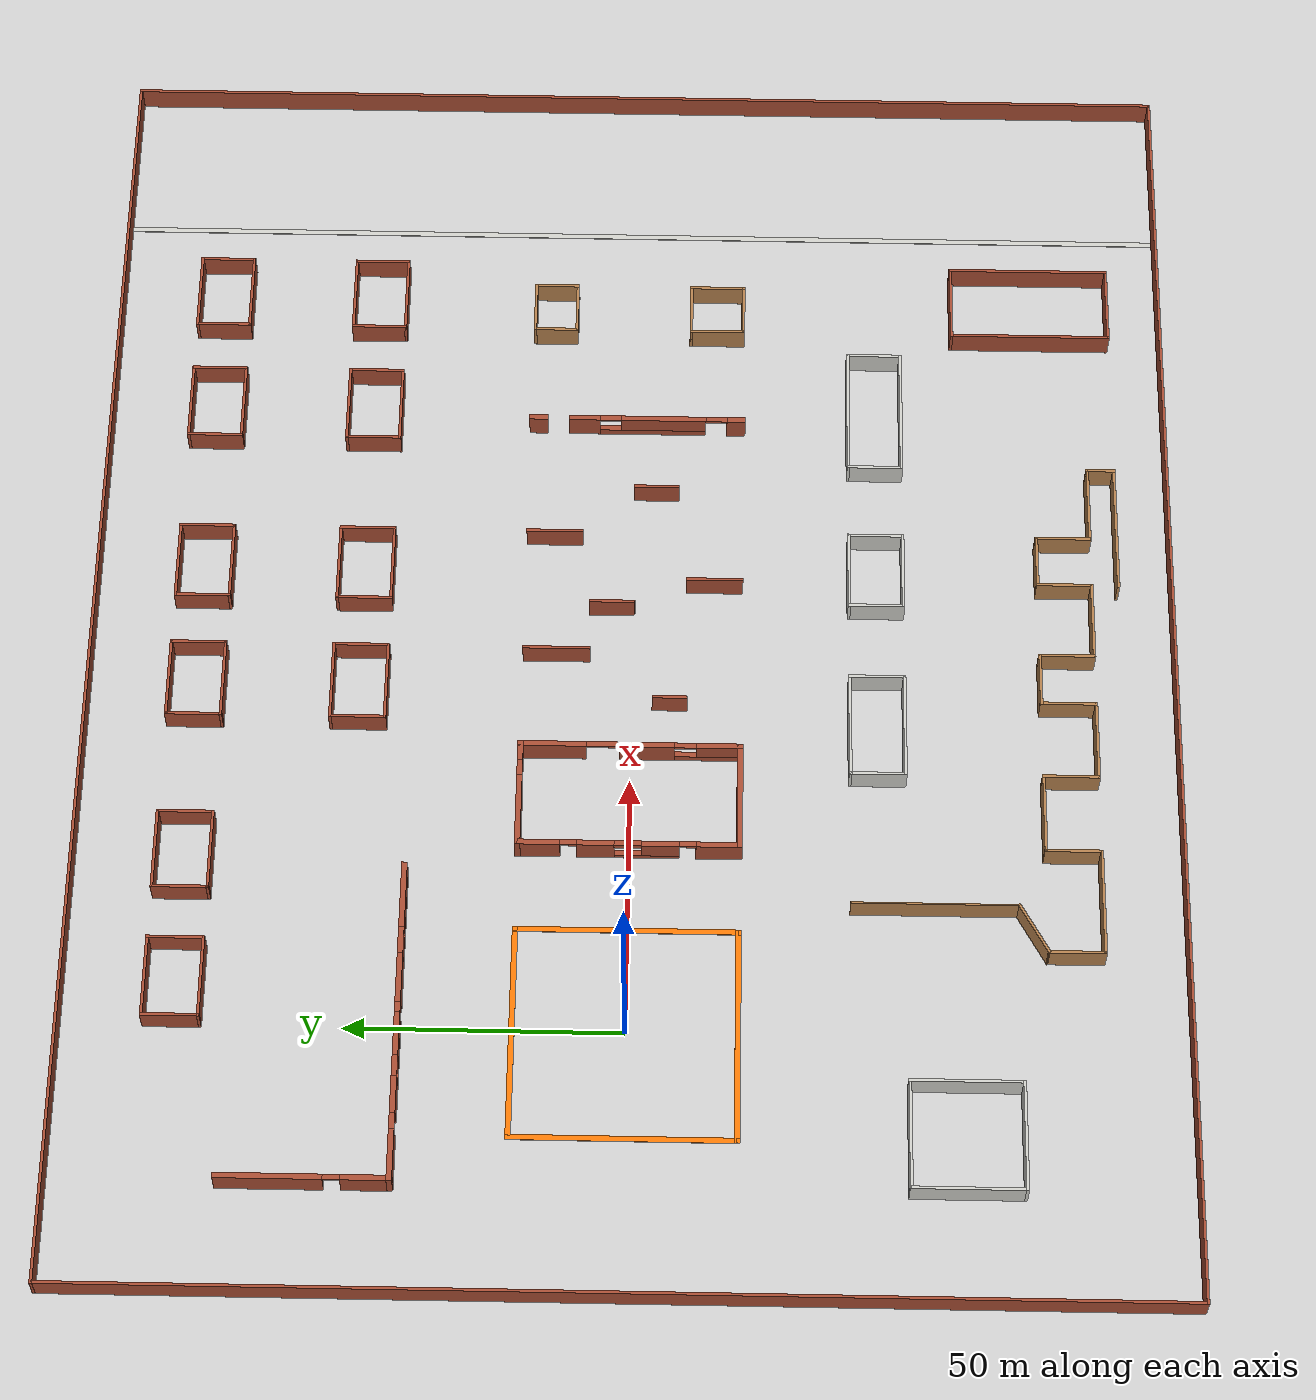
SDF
<sdf version="1.6">
 <world name="indoor6">
  <plugin name="gz::sim::systems::Physics" filename="gz-sim-physics-system"/>
  <plugin name="gz::sim::systems::UserCommands" filename="gz-sim-user-commands-system"/>
  <plugin name="gz::sim::systems::SceneBroadcaster" filename="gz-sim-scene-broadcaster-system"/>
  <plugin name="gz::sim::systems::Contact" filename="gz-sim-contact-system"/>
  <plugin name="gz::sim::systems::Imu" filename="gz-sim-imu-system"/>
  <plugin name="gz::sim::systems::AirPressure" filename="gz-sim-air-pressure-system"/>
  <plugin name="gz::sim::systems::ApplyLinkWrench" filename="gz-sim-apply-link-wrench-system"/>
  <plugin name="gz::sim::systems::NavSat" filename="gz-sim-navsat-system"/>
  <plugin name="gz::sim::systems::Sensors" filename="gz-sim-sensors-system">
   <render_engine>ogre2</render_engine>
  </plugin>
  <light name="sun" type="directional">
   <pose>0 0 10 0 -0 0</pose>
   <diffuse>0.8 0.8 0.8 1</diffuse>
   <specular>0.2 0.2 0.2 1</specular>
   <attenuation>
    <range>1000</range>
    <constant>0.9</constant>
    <linear>0.01</linear>
    <quadratic>0.001</quadratic>
   </attenuation>
   <direction>-0.5 0.1 -0.9</direction>
  </light>
  <model name="ground_plane">
   <static>1</static>
   <link name="link">
    <collision name="collision">
     <geometry><plane><normal>0 0 1</normal><size>100 100</size></plane></geometry>
     <surface><friction><ode><mu>100</mu><mu2>50</mu2></ode></friction></surface>
    </collision>
    <visual name="visual">
     <cast_shadows>0</cast_shadows>
     <geometry><plane><normal>0 0 1</normal><size>100 100</size></plane></geometry>
     <material>
      <script><uri>file://media/materials/scripts/gazebo.material</uri><name>Gazebo/Grey</name></script>
     </material>
    </visual>
   </link>
  </model>
  <gravity>0 0 -9.8</gravity>
  <magnetic_field>6e-06 2.3e-05 -4.2e-05</magnetic_field>
  <atmosphere type="adiabatic"/>
  <physics name="default_physics" default="0" type="ode">
   <max_step_size>0.001</max_step_size>
   <real_time_factor>1</real_time_factor>
   <real_time_update_rate>1000</real_time_update_rate>
  </physics>
  <scene><ambient>0.4 0.4 0.4 1</ambient><background>0.7 0.7 0.7 1</background><shadows>1</shadows></scene>
  <audio><device>default</device></audio>
  <spherical_coordinates>
   <surface_model>EARTH_WGS84</surface_model>
   <latitude_deg>0</latitude_deg>
   <longitude_deg>0</longitude_deg>
   <elevation>0</elevation>
   <heading_deg>0</heading_deg>
  </spherical_coordinates>
  <model name="Playground">
   <pose>75 0 0 0 -0 0</pose>
   <link name="Wall_0">
    <collision name="Wall_0_Collision">
     <geometry><box><size>200.5 0.5 5</size></box></geometry>
     <pose>0 0 2.5 0 -0 0</pose>
    </collision>
    <visual name="Wall_0_Visual">
     <pose>0 0 2.5 0 -0 0</pose>
     <geometry><box><size>200.5 0.5 5</size></box></geometry>
     <material>
      <script><uri>file://media/materials/scripts/gazebo.material</uri><name>Gazebo/Bricks</name></script>
      <ambient>1 1 1 1</ambient>
     </material>
     <meta><layer>0</layer></meta>
    </visual>
    <pose>-125 0 0 0 -0 -1.5708</pose>
   </link>
   <link name="Wall_1">
    <collision name="Wall_1_Collision">
     <geometry><box><size>250.5 0.5 5</size></box></geometry>
     <pose>0 0 2.5 0 -0 0</pose>
    </collision>
    <visual name="Wall_1_Visual">
     <pose>0 0 2.5 0 -0 0</pose>
     <geometry><box><size>250.5 0.5 5</size></box></geometry>
     <material>
      <script><uri>file://media/materials/scripts/gazebo.material</uri><name>Gazebo/Bricks</name></script>
      <ambient>1 1 1 1</ambient>
     </material>
     <meta><layer>0</layer></meta>
    </visual>
    <pose>-2e-06 -100 0 0 -0 0</pose>
   </link>
   <link name="Wall_11">
    <pose>-40 0 0 0 -0 -1.5708</pose>
    <visual name="Wall_11_Visual_0">
     <pose>-16.411 0 2.5 0 -0 0</pose>
     <geometry><box><size>8.17799 1 5</size></box></geometry>
     <material>
      <script><uri>file://media/materials/scripts/gazebo.material</uri><name>Gazebo/Bricks</name></script>
      <ambient>1 1 1 1</ambient>
     </material>
     <meta><layer>0</layer></meta>
    </visual>
    <collision name="Wall_11_Collision_0">
     <geometry><box><size>8.17799 1 5</size></box></geometry>
     <pose>-16.411 0 2.5 0 -0 0</pose>
    </collision>
    <visual name="Wall_11_Visual_1">
     <pose>-5.95363 0 2.5 0 -0 0</pose>
     <geometry><box><size>6.73676 1 5</size></box></geometry>
     <material>
      <script><uri>file://media/materials/scripts/gazebo.material</uri><name>Gazebo/Bricks</name></script>
      <ambient>1 1 1 1</ambient>
     </material>
     <meta><layer>0</layer></meta>
    </visual>
    <collision name="Wall_11_Collision_1">
     <geometry><box><size>6.73676 1 5</size></box></geometry>
     <pose>-5.95363 0 2.5 0 -0 0</pose>
    </collision>
    <visual name="Wall_11_Visual_2">
     <pose>16.3258 0 2.5 0 -0 0</pose>
     <geometry><box><size>8.34849 1 5</size></box></geometry>
     <material>
      <script><uri>file://media/materials/scripts/gazebo.material</uri><name>Gazebo/Bricks</name></script>
      <ambient>1 1 1 1</ambient>
     </material>
     <meta><layer>0</layer></meta>
    </visual>
    <collision name="Wall_11_Collision_2">
     <geometry><box><size>8.34849 1 5</size></box></geometry>
     <pose>16.3258 0 2.5 0 -0 0</pose>
    </collision>
    <visual name="Wall_11_Visual_3">
     <pose>3.28313 0 0.5 0 -0 0</pose>
     <geometry><box><size>11.7368 1 1</size></box></geometry>
     <material>
      <script><uri>file://media/materials/scripts/gazebo.material</uri><name>Gazebo/Bricks</name></script>
      <ambient>1 1 1 1</ambient>
     </material>
     <meta><layer>0</layer></meta>
    </visual>
    <collision name="Wall_11_Collision_3">
     <geometry><box><size>11.7368 1 1</size></box></geometry>
     <pose>3.28313 0 0.5 0 -0 0</pose>
    </collision>
    <visual name="Wall_11_Visual_4">
     <pose>5.78313 0 3 0 -0 0</pose>
     <geometry><box><size>6.73676 1 4</size></box></geometry>
     <material>
      <script><uri>file://media/materials/scripts/gazebo.material</uri><name>Gazebo/Bricks</name></script>
      <ambient>1 1 1 1</ambient>
     </material>
     <meta><layer>0</layer></meta>
    </visual>
    <collision name="Wall_11_Collision_4">
     <geometry><box><size>6.73676 1 4</size></box></geometry>
     <pose>5.78313 0 3 0 -0 0</pose>
    </collision>
    <visual name="Wall_11_Visual_5">
     <pose>-0.08525 0 4.5 0 -0 0</pose>
     <geometry><box><size>5 1 1</size></box></geometry>
     <material>
      <script><uri>file://media/materials/scripts/gazebo.material</uri><name>Gazebo/Bricks</name></script>
      <ambient>1 1 1 1</ambient>
     </material>
     <meta><layer>0</layer></meta>
    </visual>
    <collision name="Wall_11_Collision_5">
     <geometry><box><size>5 1 1</size></box></geometry>
     <pose>-0.08525 0 4.5 0 -0 0</pose>
    </collision>
    <visual name="Wall_11_Visual_6">
     <pose>-10.822 0 4.75 0 -0 0</pose>
     <geometry><box><size>3 1 0.5</size></box></geometry>
     <material>
      <script><uri>file://media/materials/scripts/gazebo.material</uri><name>Gazebo/Bricks</name></script>
      <ambient>1 1 1 1</ambient>
     </material>
     <meta><layer>0</layer></meta>
    </visual>
    <collision name="Wall_11_Collision_6">
     <geometry><box><size>3 1 0.5</size></box></geometry>
     <pose>-10.822 0 4.75 0 -0 0</pose>
    </collision>
    <visual name="Wall_11_Visual_7">
     <pose>10.6515 0 4.75 0 -0 0</pose>
     <geometry><box><size>3 1 0.5</size></box></geometry>
     <material>
      <script><uri>file://media/materials/scripts/gazebo.material</uri><name>Gazebo/Bricks</name></script>
      <ambient>1 1 1 1</ambient>
     </material>
     <meta><layer>0</layer></meta>
    </visual>
    <collision name="Wall_11_Collision_7">
     <geometry><box><size>3 1 0.5</size></box></geometry>
     <pose>10.6515 0 4.75 0 -0 0</pose>
    </collision>
   </link>
   <link name="Wall_133">
    <pose>-75 40 0 0 -0 0</pose>
    <visual name="Wall_133_Visual_0">
     <pose>-25.689 0 2.5 0 -0 0</pose>
     <geometry><box><size>9.62192 1 5</size></box></geometry>
     <material>
      <script><uri>file://media/materials/scripts/gazebo.material</uri><name>Gazebo/Bricks</name></script>
      <ambient>1 1 1 1</ambient>
     </material>
     <meta><layer>0</layer></meta>
    </visual>
    <collision name="Wall_133_Collision_0">
     <geometry><box><size>9.62192 1 5</size></box></geometry>
     <pose>-25.689 0 2.5 0 -0 0</pose>
    </collision>
    <visual name="Wall_133_Visual_1">
     <pose>-14.3919 0 2.5 0 -0 0</pose>
     <geometry><box><size>6.97234 1 5</size></box></geometry>
     <material>
      <script><uri>file://media/materials/scripts/gazebo.material</uri><name>Gazebo/Bricks</name></script>
      <ambient>1 1 1 1</ambient>
     </material>
     <meta><layer>0</layer></meta>
    </visual>
    <collision name="Wall_133_Collision_1">
     <geometry><box><size>6.97234 1 5</size></box></geometry>
     <pose>-14.3919 0 2.5 0 -0 0</pose>
    </collision>
    <visual name="Wall_133_Visual_2">
     <pose>7.95331 0 2.5 0 -0 0</pose>
     <geometry><box><size>9.53225 1 5</size></box></geometry>
     <material>
      <script><uri>file://media/materials/scripts/gazebo.material</uri><name>Gazebo/Bricks</name></script>
      <ambient>1 1 1 1</ambient>
     </material>
     <meta><layer>0</layer></meta>
    </visual>
    <collision name="Wall_133_Collision_2">
     <geometry><box><size>9.53225 1 5</size></box></geometry>
     <pose>7.95331 0 2.5 0 -0 0</pose>
    </collision>
    <visual name="Wall_133_Visual_3">
     <pose>-4.85928 0 0.75 0 -0 0</pose>
     <geometry><box><size>12.0929 1 1.5</size></box></geometry>
     <material>
      <script><uri>file://media/materials/scripts/gazebo.material</uri><name>Gazebo/Bricks</name></script>
      <ambient>1 1 1 1</ambient>
     </material>
     <meta><layer>0</layer></meta>
    </visual>
    <collision name="Wall_133_Collision_3">
     <geometry><box><size>12.0929 1 1.5</size></box></geometry>
     <pose>-4.85928 0 0.75 0 -0 0</pose>
    </collision>
    <visual name="Wall_133_Visual_4">
     <pose>21.6097 0 0.75 0 -0 0</pose>
     <geometry><box><size>17.7806 1 1.5</size></box></geometry>
     <material>
      <script><uri>file://media/materials/scripts/gazebo.material</uri><name>Gazebo/Bricks</name></script>
      <ambient>1 1 1 1</ambient>
     </material>
     <meta><layer>0</layer></meta>
    </visual>
    <collision name="Wall_133_Collision_4">
     <geometry><box><size>17.7806 1 1.5</size></box></geometry>
     <pose>21.6097 0 0.75 0 -0 0</pose>
    </collision>
    <visual name="Wall_133_Visual_5">
     <pose>-2.85928 0 3.25 0 -0 0</pose>
     <geometry><box><size>8.09293 1 3.5</size></box></geometry>
     <material>
      <script><uri>file://media/materials/scripts/gazebo.material</uri><name>Gazebo/Bricks</name></script>
      <ambient>1 1 1 1</ambient>
     </material>
     <meta><layer>0</layer></meta>
    </visual>
    <collision name="Wall_133_Collision_5">
     <geometry><box><size>8.09293 1 3.5</size></box></geometry>
     <pose>-2.85928 0 3.25 0 -0 0</pose>
    </collision>
    <visual name="Wall_133_Visual_6">
     <pose>-2.85928 0 3.25 0 -0 0</pose>
     <geometry><box><size>8.09293 1 3.5</size></box></geometry>
     <material>
      <script><uri>file://media/materials/scripts/gazebo.material</uri><name>Gazebo/Bricks</name></script>
      <ambient>1 1 1 1</ambient>
     </material>
     <meta><layer>0</layer></meta>
    </visual>
    <collision name="Wall_133_Collision_6">
     <geometry><box><size>8.09293 1 3.5</size></box></geometry>
     <pose>-2.85928 0 3.25 0 -0 0</pose>
    </collision>
    <visual name="Wall_133_Visual_7">
     <pose>24.1097 0 3.25 0 -0 0</pose>
     <geometry><box><size>12.7806 1 3.5</size></box></geometry>
     <material>
      <script><uri>file://media/materials/scripts/gazebo.material</uri><name>Gazebo/Bricks</name></script>
      <ambient>1 1 1 1</ambient>
     </material>
     <meta><layer>0</layer></meta>
    </visual>
    <collision name="Wall_133_Collision_7">
     <geometry><box><size>12.7806 1 3.5</size></box></geometry>
     <pose>24.1097 0 3.25 0 -0 0</pose>
    </collision>
    <visual name="Wall_133_Visual_8">
     <pose>2.18719 0 4.5 0 -0 0</pose>
     <geometry><box><size>2 1 1</size></box></geometry>
     <material>
      <script><uri>file://media/materials/scripts/gazebo.material</uri><name>Gazebo/Bricks</name></script>
      <ambient>1 1 1 1</ambient>
     </material>
     <meta><layer>0</layer></meta>
    </visual>
    <collision name="Wall_133_Collision_8">
     <geometry><box><size>2 1 1</size></box></geometry>
     <pose>2.18719 0 4.5 0 -0 0</pose>
    </collision>
    <visual name="Wall_133_Visual_9">
     <pose>2.18719 0 4.5 0 -0 0</pose>
     <geometry><box><size>2 1 1</size></box></geometry>
     <material>
      <script><uri>file://media/materials/scripts/gazebo.material</uri><name>Gazebo/Bricks</name></script>
      <ambient>1 1 1 1</ambient>
     </material>
     <meta><layer>0</layer></meta>
    </visual>
    <collision name="Wall_133_Collision_9">
     <geometry><box><size>2 1 1</size></box></geometry>
     <pose>2.18719 0 4.5 0 -0 0</pose>
    </collision>
    <visual name="Wall_133_Visual_10">
     <pose>-19.3781 0 4.75 0 -0 0</pose>
     <geometry><box><size>3 1 0.5</size></box></geometry>
     <material>
      <script><uri>file://media/materials/scripts/gazebo.material</uri><name>Gazebo/Bricks</name></script>
      <ambient>1 1 1 1</ambient>
     </material>
     <meta><layer>0</layer></meta>
    </visual>
    <collision name="Wall_133_Collision_10">
     <geometry><box><size>3 1 0.5</size></box></geometry>
     <pose>-19.3781 0 4.75 0 -0 0</pose>
    </collision>
    <visual name="Wall_133_Visual_11">
     <pose>-8.90574 0 4.75 0 -0 0</pose>
     <geometry><box><size>4 1 0.5</size></box></geometry>
     <material>
      <script><uri>file://media/materials/scripts/gazebo.material</uri><name>Gazebo/Bricks</name></script>
      <ambient>1 1 1 1</ambient>
     </material>
     <meta><layer>0</layer></meta>
    </visual>
    <collision name="Wall_133_Collision_11">
     <geometry><box><size>4 1 0.5</size></box></geometry>
     <pose>-8.90574 0 4.75 0 -0 0</pose>
    </collision>
    <visual name="Wall_133_Visual_12">
     <pose>15.2194 0 4.75 0 -0 0</pose>
     <geometry><box><size>5 1 0.5</size></box></geometry>
     <material>
      <script><uri>file://media/materials/scripts/gazebo.material</uri><name>Gazebo/Bricks</name></script>
      <ambient>1 1 1 1</ambient>
     </material>
     <meta><layer>0</layer></meta>
    </visual>
    <collision name="Wall_133_Collision_12">
     <geometry><box><size>5 1 0.5</size></box></geometry>
     <pose>15.2194 0 4.75 0 -0 0</pose>
    </collision>
   </link>
   <link name="Wall_135">
    <collision name="Wall_135_Collision">
     <geometry><box><size>30.25 0.25 5</size></box></geometry>
     <pose>0 0 2.5 0 -0 0</pose>
    </collision>
    <visual name="Wall_135_Visual">
     <pose>0 0 2.5 0 -0 0</pose>
     <geometry><box><size>30.25 0.25 5</size></box></geometry>
     <material>
      <script><uri>file://media/materials/scripts/gazebo.material</uri><name>Gazebo/Wood</name></script>
      <ambient>1 1 1 1</ambient>
     </material>
     <meta><layer>0</layer></meta>
    </visual>
    <pose>-51 -55 0 0 -0 -1.5708</pose>
   </link>
   <link name="Wall_136">
    <collision name="Wall_136_Collision">
     <geometry><box><size>10.7956 0.5 5</size></box></geometry>
     <pose>0 0 2.5 0 -0 0</pose>
    </collision>
    <visual name="Wall_136_Visual">
     <pose>0 0 2.5 0 -0 0</pose>
     <geometry><box><size>10.7956 0.5 5</size></box></geometry>
     <material>
      <script><uri>file://media/materials/scripts/gazebo.material</uri><name>Gazebo/Wood</name></script>
      <ambient>1 1 1 1</ambient>
     </material>
     <meta><layer>0</layer></meta>
    </visual>
    <pose>-55.5 -72.5 0 0 -0 -2.63449</pose>
   </link>
   <link name="Wall_137">
    <collision name="Wall_137_Collision">
     <geometry><box><size>10.5 0.5 5</size></box></geometry>
     <pose>0 0 2.5 0 -0 0</pose>
    </collision>
    <visual name="Wall_137_Visual">
     <pose>0 0 2.5 0 -0 0</pose>
     <geometry><box><size>10.5 0.5 5</size></box></geometry>
     <material>
      <script><uri>file://media/materials/scripts/gazebo.material</uri><name>Gazebo/Wood</name></script>
      <ambient>1 1 1 1</ambient>
     </material>
     <meta><layer>0</layer></meta>
    </visual>
    <pose>-60 -80 0 0 -0 -1.5708</pose>
   </link>
   <link name="Wall_138">
    <collision name="Wall_138_Collision">
     <geometry><box><size>20.5 0.5 5</size></box></geometry>
     <pose>0 0 2.5 0 -0 0</pose>
    </collision>
    <visual name="Wall_138_Visual">
     <pose>0 0 2.5 0 -0 0</pose>
     <geometry><box><size>20.5 0.5 5</size></box></geometry>
     <material>
      <script><uri>file://media/materials/scripts/gazebo.material</uri><name>Gazebo/Wood</name></script>
      <ambient>1 1 1 1</ambient>
     </material>
     <meta><layer>0</layer></meta>
    </visual>
    <pose>-50 -85 0 0 -0 0</pose>
   </link>
   <link name="Wall_139">
    <collision name="Wall_139_Collision">
     <geometry><box><size>10.5 0.5 5</size></box></geometry>
     <pose>0 0 2.5 0 -0 0</pose>
    </collision>
    <visual name="Wall_139_Visual">
     <pose>0 0 2.5 0 -0 0</pose>
     <geometry><box><size>10.5 0.5 5</size></box></geometry>
     <material>
      <script><uri>file://media/materials/scripts/gazebo.material</uri><name>Gazebo/Wood</name></script>
      <ambient>1 1 1 1</ambient>
     </material>
     <meta><layer>0</layer></meta>
    </visual>
    <pose>-40 -80 0 0 -0 1.5708</pose>
   </link>
   <link name="Wall_140">
    <collision name="Wall_140_Collision">
     <geometry><box><size>15.5 0.5 5</size></box></geometry>
     <pose>0 0 2.5 0 -0 0</pose>
    </collision>
    <visual name="Wall_140_Visual">
     <pose>0 0 2.5 0 -0 0</pose>
     <geometry><box><size>15.5 0.5 5</size></box></geometry>
     <material>
      <script><uri>file://media/materials/scripts/gazebo.material</uri><name>Gazebo/Wood</name></script>
      <ambient>1 1 1 1</ambient>
     </material>
     <meta><layer>0</layer></meta>
    </visual>
    <pose>-32.5 -75 0 0 -0 0</pose>
   </link>
   <link name="Wall_141">
    <collision name="Wall_141_Collision">
     <geometry><box><size>10.5 0.5 5</size></box></geometry>
     <pose>0 0 2.5 0 -0 0</pose>
    </collision>
    <visual name="Wall_141_Visual">
     <pose>0 0 2.5 0 -0 0</pose>
     <geometry><box><size>10.5 0.5 5</size></box></geometry>
     <material>
      <script><uri>file://media/materials/scripts/gazebo.material</uri><name>Gazebo/Wood</name></script>
      <ambient>1 1 1 1</ambient>
     </material>
     <meta><layer>0</layer></meta>
    </visual>
    <pose>-25 -80 0 0 -0 -1.5708</pose>
   </link>
   <link name="Wall_142">
    <collision name="Wall_142_Collision">
     <geometry><box><size>15.5 0.5 5</size></box></geometry>
     <pose>0 0 2.5 0 -0 0</pose>
    </collision>
    <visual name="Wall_142_Visual">
     <pose>0 0 2.5 0 -0 0</pose>
     <geometry><box><size>15.5 0.5 5</size></box></geometry>
     <material>
      <script><uri>file://media/materials/scripts/gazebo.material</uri><name>Gazebo/Wood</name></script>
      <ambient>1 1 1 1</ambient>
     </material>
     <meta><layer>0</layer></meta>
    </visual>
    <pose>-17.5 -85 0 0 -0 0</pose>
   </link>
   <link name="Wall_143">
    <collision name="Wall_143_Collision">
     <geometry><box><size>10.5 0.5 5</size></box></geometry>
     <pose>0 0 2.5 0 -0 0</pose>
    </collision>
    <visual name="Wall_143_Visual">
     <pose>0 0 2.5 0 -0 0</pose>
     <geometry><box><size>10.5 0.5 5</size></box></geometry>
     <material>
      <script><uri>file://media/materials/scripts/gazebo.material</uri><name>Gazebo/Wood</name></script>
      <ambient>1 1 1 1</ambient>
     </material>
     <meta><layer>0</layer></meta>
    </visual>
    <pose>-10 -80 0 0 -0 1.5708</pose>
   </link>
   <link name="Wall_144">
    <collision name="Wall_144_Collision">
     <geometry><box><size>10.5 0.5 5</size></box></geometry>
     <pose>0 0 2.5 0 -0 0</pose>
    </collision>
    <visual name="Wall_144_Visual">
     <pose>0 0 2.5 0 -0 0</pose>
     <geometry><box><size>10.5 0.5 5</size></box></geometry>
     <material>
      <script><uri>file://media/materials/scripts/gazebo.material</uri><name>Gazebo/Wood</name></script>
      <ambient>1 1 1 1</ambient>
     </material>
     <meta><layer>0</layer></meta>
    </visual>
    <pose>-5 -75 0 0 -0 0</pose>
   </link>
   <link name="Wall_145">
    <collision name="Wall_145_Collision">
     <geometry><box><size>10.5 0.5 5</size></box></geometry>
     <pose>0 0 2.5 0 -0 0</pose>
    </collision>
    <visual name="Wall_145_Visual">
     <pose>0 0 2.5 0 -0 0</pose>
     <geometry><box><size>10.5 0.5 5</size></box></geometry>
     <material>
      <script><uri>file://media/materials/scripts/gazebo.material</uri><name>Gazebo/Wood</name></script>
      <ambient>1 1 1 1</ambient>
     </material>
     <meta><layer>0</layer></meta>
    </visual>
    <pose>-2e-06 -80 0 0 -0 -1.5708</pose>
   </link>
   <link name="Wall_146">
    <collision name="Wall_146_Collision">
     <geometry><box><size>15.5 0.5 5</size></box></geometry>
     <pose>0 0 2.5 0 -0 0</pose>
    </collision>
    <visual name="Wall_146_Visual">
     <pose>0 0 2.5 0 -0 0</pose>
     <geometry><box><size>15.5 0.5 5</size></box></geometry>
     <material>
      <script><uri>file://media/materials/scripts/gazebo.material</uri><name>Gazebo/Wood</name></script>
      <ambient>1 1 1 1</ambient>
     </material>
     <meta><layer>0</layer></meta>
    </visual>
    <pose>7.5 -85 0 0 -0 0</pose>
   </link>
   <link name="Wall_147">
    <collision name="Wall_147_Collision">
     <geometry><box><size>10.5 0.5 5</size></box></geometry>
     <pose>0 0 2.5 0 -0 0</pose>
    </collision>
    <visual name="Wall_147_Visual">
     <pose>0 0 2.5 0 -0 0</pose>
     <geometry><box><size>10.5 0.5 5</size></box></geometry>
     <material>
      <script><uri>file://media/materials/scripts/gazebo.material</uri><name>Gazebo/Wood</name></script>
      <ambient>1 1 1 1</ambient>
     </material>
     <meta><layer>0</layer></meta>
    </visual>
    <pose>15 -80 0 0 -0 1.5708</pose>
   </link>
   <link name="Wall_148">
    <collision name="Wall_148_Collision">
     <geometry><box><size>10.5 0.5 5</size></box></geometry>
     <pose>0 0 2.5 0 -0 0</pose>
    </collision>
    <visual name="Wall_148_Visual">
     <pose>0 0 2.5 0 -0 0</pose>
     <geometry><box><size>10.5 0.5 5</size></box></geometry>
     <material>
      <script><uri>file://media/materials/scripts/gazebo.material</uri><name>Gazebo/Wood</name></script>
      <ambient>1 1 1 1</ambient>
     </material>
     <meta><layer>0</layer></meta>
    </visual>
    <pose>20 -75 0 0 -0 0</pose>
   </link>
   <link name="Wall_149">
    <collision name="Wall_149_Collision">
     <geometry><box><size>10.5 0.5 5</size></box></geometry>
     <pose>0 0 2.5 0 -0 0</pose>
    </collision>
    <visual name="Wall_149_Visual">
     <pose>0 0 2.5 0 -0 0</pose>
     <geometry><box><size>10.5 0.5 5</size></box></geometry>
     <material>
      <script><uri>file://media/materials/scripts/gazebo.material</uri><name>Gazebo/Wood</name></script>
      <ambient>1 1 1 1</ambient>
     </material>
     <meta><layer>0</layer></meta>
    </visual>
    <pose>25 -80 0 0 -0 -1.5708</pose>
   </link>
   <link name="Wall_15">
    <pose>-30 20 0 0 -0 0</pose>
    <visual name="Wall_15_Visual_0">
     <pose>-3.5 0 2.5 0 -0 0</pose>
     <geometry><box><size>14 1 5</size></box></geometry>
     <material>
      <script><uri>file://media/materials/scripts/gazebo.material</uri><name>Gazebo/Bricks</name></script>
      <ambient>1 1 1 1</ambient>
     </material>
     <meta><layer>0</layer></meta>
    </visual>
    <collision name="Wall_15_Collision_0">
     <geometry><box><size>14 1 5</size></box></geometry>
     <pose>-3.5 0 2.5 0 -0 0</pose>
    </collision>
    <visual name="Wall_15_Visual_1">
     <pose>8.5 0 2.5 0 -0 0</pose>
     <geometry><box><size>4 1 5</size></box></geometry>
     <material>
      <script><uri>file://media/materials/scripts/gazebo.material</uri><name>Gazebo/Bricks</name></script>
      <ambient>1 1 1 1</ambient>
     </material>
     <meta><layer>0</layer></meta>
    </visual>
    <collision name="Wall_15_Collision_1">
     <geometry><box><size>4 1 5</size></box></geometry>
     <pose>8.5 0 2.5 0 -0 0</pose>
    </collision>
    <visual name="Wall_15_Visual_2">
     <pose>5 0 4.75 0 -0 0</pose>
     <geometry><box><size>3 1 0.5</size></box></geometry>
     <material>
      <script><uri>file://media/materials/scripts/gazebo.material</uri><name>Gazebo/Bricks</name></script>
      <ambient>1 1 1 1</ambient>
     </material>
     <meta><layer>0</layer></meta>
    </visual>
    <collision name="Wall_15_Collision_2">
     <geometry><box><size>3 1 0.5</size></box></geometry>
     <pose>5 0 4.75 0 -0 0</pose>
    </collision>
   </link>
   <link name="Wall_150">
    <collision name="Wall_150_Collision">
     <geometry><box><size>15.5 0.5 5</size></box></geometry>
     <pose>0 0 2.5 0 -0 0</pose>
    </collision>
    <visual name="Wall_150_Visual">
     <pose>0 0 2.5 0 -0 0</pose>
     <geometry><box><size>15.5 0.5 5</size></box></geometry>
     <material>
      <script><uri>file://media/materials/scripts/gazebo.material</uri><name>Gazebo/Wood</name></script>
      <ambient>1 1 1 1</ambient>
     </material>
     <meta><layer>0</layer></meta>
    </visual>
    <pose>32.5 -85 0 0 -0 0</pose>
   </link>
   <link name="Wall_151">
    <collision name="Wall_151_Collision">
     <geometry><box><size>5.5 0.5 5</size></box></geometry>
     <pose>0 0 2.5 0 -0 0</pose>
    </collision>
    <visual name="Wall_151_Visual">
     <pose>0 0 2.5 0 -0 0</pose>
     <geometry><box><size>5.5 0.5 5</size></box></geometry>
     <material>
      <script><uri>file://media/materials/scripts/gazebo.material</uri><name>Gazebo/Wood</name></script>
      <ambient>1 1 1 1</ambient>
     </material>
     <meta><layer>0</layer></meta>
    </visual>
    <pose>40 -87.5 0 0 -0 -1.5708</pose>
   </link>
   <link name="Wall_152">
    <collision name="Wall_152_Collision">
     <geometry><box><size>25.5 0.5 5</size></box></geometry>
     <pose>0 0 2.5 0 -0 0</pose>
    </collision>
    <visual name="Wall_152_Visual">
     <pose>0 0 2.5 0 -0 0</pose>
     <geometry><box><size>25.5 0.5 5</size></box></geometry>
     <material>
      <script><uri>file://media/materials/scripts/gazebo.material</uri><name>Gazebo/Wood</name></script>
      <ambient>1 1 1 1</ambient>
     </material>
     <meta><layer>0</layer></meta>
    </visual>
    <pose>27.5 -90 0 0 -0 3.14159</pose>
   </link>
   <link name="Wall_154">
    <collision name="Wall_154_Collision">
     <geometry><box><size>20.5 0.5 5</size></box></geometry>
     <pose>0 0 2.5 0 -0 0</pose>
    </collision>
    <visual name="Wall_154_Visual">
     <pose>0 0 2.5 0 -0 0</pose>
     <geometry><box><size>20.5 0.5 5</size></box></geometry>
     <material>
      <script><uri>file://media/materials/scripts/gazebo.material</uri><name>Gazebo/CeilingTiled</name></script>
      <ambient>1 0.764706 0.305882 1</ambient>
     </material>
     <meta><layer>0</layer></meta>
    </visual>
    <pose>-95 -50 0 0 -0 0</pose>
   </link>
   <link name="Wall_155">
    <collision name="Wall_155_Collision">
     <geometry><box><size>20.5 0.5 5</size></box></geometry>
     <pose>0 0 2.5 0 -0 0</pose>
    </collision>
    <visual name="Wall_155_Visual">
     <pose>0 0 2.5 0 -0 0</pose>
     <geometry><box><size>20.5 0.5 5</size></box></geometry>
     <material>
      <script><uri>file://media/materials/scripts/gazebo.material</uri><name>Gazebo/CeilingTiled</name></script>
      <ambient>1 0.764706 0.305882 1</ambient>
     </material>
     <meta><layer>0</layer></meta>
    </visual>
    <pose>-85 -60 0 0 -0 -1.5708</pose>
   </link>
   <link name="Wall_156">
    <collision name="Wall_156_Collision">
     <geometry><box><size>20.5 0.5 5</size></box></geometry>
     <pose>0 0 2.5 0 -0 0</pose>
    </collision>
    <visual name="Wall_156_Visual">
     <pose>0 0 2.5 0 -0 0</pose>
     <geometry><box><size>20.5 0.5 5</size></box></geometry>
     <material>
      <script><uri>file://media/materials/scripts/gazebo.material</uri><name>Gazebo/CeilingTiled</name></script>
      <ambient>1 0.764706 0.305882 1</ambient>
     </material>
     <meta><layer>0</layer></meta>
    </visual>
    <pose>-95 -70 0 0 -0 3.14159</pose>
   </link>
   <link name="Wall_157">
    <collision name="Wall_157_Collision">
     <geometry><box><size>20.5 0.5 5</size></box></geometry>
     <pose>0 0 2.5 0 -0 0</pose>
    </collision>
    <visual name="Wall_157_Visual">
     <pose>0 0 2.5 0 -0 0</pose>
     <geometry><box><size>20.5 0.5 5</size></box></geometry>
     <material>
      <script><uri>file://media/materials/scripts/gazebo.material</uri><name>Gazebo/CeilingTiled</name></script>
      <ambient>1 0.764706 0.305882 1</ambient>
     </material>
     <meta><layer>0</layer></meta>
    </visual>
    <pose>-105 -60 0 0 -0 1.5708</pose>
   </link>
   <link name="Wall_159">
    <collision name="Wall_159_Collision">
     <geometry><box><size>10.5 0.5 5</size></box></geometry>
     <pose>0 0 2.5 0 -0 0</pose>
    </collision>
    <visual name="Wall_159_Visual">
     <pose>0 0 2.5 0 -0 0</pose>
     <geometry><box><size>10.5 0.5 5</size></box></geometry>
     <material>
      <script><uri>file://media/materials/scripts/gazebo.material</uri><name>Gazebo/CeilingTiled</name></script>
      <ambient>0.435294 0.796078 0.67451 1</ambient>
     </material>
     <meta><layer>0</layer></meta>
    </visual>
    <pose>-25 -45 0 0 -0 -1.5708</pose>
   </link>
   <link name="Wall_16">
    <pose>-20 0 0 0 -0 -1.5708</pose>
    <visual name="Wall_16_Visual_0">
     <pose>-14.25 0 2.5 0 -0 0</pose>
     <geometry><box><size>12.5 1 5</size></box></geometry>
     <material>
      <script><uri>file://media/materials/scripts/gazebo.material</uri><name>Gazebo/Bricks</name></script>
      <ambient>1 1 1 1</ambient>
     </material>
     <meta><layer>0</layer></meta>
    </visual>
    <collision name="Wall_16_Collision_0">
     <geometry><box><size>12.5 1 5</size></box></geometry>
     <pose>-14.25 0 2.5 0 -0 0</pose>
    </collision>
    <visual name="Wall_16_Visual_1">
     <pose>3 0 2.5 0 -0 0</pose>
     <geometry><box><size>10 1 5</size></box></geometry>
     <material>
      <script><uri>file://media/materials/scripts/gazebo.material</uri><name>Gazebo/Bricks</name></script>
      <ambient>1 1 1 1</ambient>
     </material>
     <meta><layer>0</layer></meta>
    </visual>
    <collision name="Wall_16_Collision_1">
     <geometry><box><size>10 1 5</size></box></geometry>
     <pose>3 0 2.5 0 -0 0</pose>
    </collision>
    <visual name="Wall_16_Visual_2">
     <pose>14.25 0 0.75 0 -0 0</pose>
     <geometry><box><size>12.5 1 1.5</size></box></geometry>
     <material>
      <script><uri>file://media/materials/scripts/gazebo.material</uri><name>Gazebo/Bricks</name></script>
      <ambient>1 1 1 1</ambient>
     </material>
     <meta><layer>0</layer></meta>
    </visual>
    <collision name="Wall_16_Collision_2">
     <geometry><box><size>12.5 1 1.5</size></box></geometry>
     <pose>14.25 0 0.75 0 -0 0</pose>
    </collision>
    <visual name="Wall_16_Visual_3">
     <pose>16.25 0 3.25 0 -0 0</pose>
     <geometry><box><size>8.5 1 3.5</size></box></geometry>
     <material>
      <script><uri>file://media/materials/scripts/gazebo.material</uri><name>Gazebo/Bricks</name></script>
      <ambient>1 1 1 1</ambient>
     </material>
     <meta><layer>0</layer></meta>
    </visual>
    <collision name="Wall_16_Collision_3">
     <geometry><box><size>8.5 1 3.5</size></box></geometry>
     <pose>16.25 0 3.25 0 -0 0</pose>
    </collision>
    <visual name="Wall_16_Visual_4">
     <pose>-5 0 4.75 0 -0 0</pose>
     <geometry><box><size>6 1 0.5</size></box></geometry>
     <material>
      <script><uri>file://media/materials/scripts/gazebo.material</uri><name>Gazebo/Bricks</name></script>
      <ambient>1 1 1 1</ambient>
     </material>
     <meta><layer>0</layer></meta>
    </visual>
    <collision name="Wall_16_Collision_4">
     <geometry><box><size>6 1 0.5</size></box></geometry>
     <pose>-5 0 4.75 0 -0 0</pose>
    </collision>
    <visual name="Wall_16_Visual_5">
     <pose>10 0 4.75 0 -0 0</pose>
     <geometry><box><size>4 1 0.5</size></box></geometry>
     <material>
      <script><uri>file://media/materials/scripts/gazebo.material</uri><name>Gazebo/Bricks</name></script>
      <ambient>1 1 1 1</ambient>
     </material>
     <meta><layer>0</layer></meta>
    </visual>
    <collision name="Wall_16_Collision_5">
     <geometry><box><size>4 1 0.5</size></box></geometry>
     <pose>10 0 4.75 0 -0 0</pose>
    </collision>
   </link>
   <link name="Wall_160">
    <collision name="Wall_160_Collision">
     <geometry><box><size>20.5 0.5 5</size></box></geometry>
     <pose>0 0 2.5 0 -0 0</pose>
    </collision>
    <visual name="Wall_160_Visual">
     <pose>0 0 2.5 0 -0 0</pose>
     <geometry><box><size>20.5 0.5 5</size></box></geometry>
     <material>
      <script><uri>file://media/materials/scripts/gazebo.material</uri><name>Gazebo/CeilingTiled</name></script>
      <ambient>0.435294 0.796078 0.67451 1</ambient>
     </material>
     <meta><layer>0</layer></meta>
    </visual>
    <pose>-15 -50 0 0 -0 0</pose>
   </link>
   <link name="Wall_161">
    <collision name="Wall_161_Collision">
     <geometry><box><size>10.5 0.5 5</size></box></geometry>
     <pose>0 0 2.5 0 -0 0</pose>
    </collision>
    <visual name="Wall_161_Visual">
     <pose>0 0 2.5 0 -0 0</pose>
     <geometry><box><size>10.5 0.5 5</size></box></geometry>
     <material>
      <script><uri>file://media/materials/scripts/gazebo.material</uri><name>Gazebo/CeilingTiled</name></script>
      <ambient>0.435294 0.796078 0.67451 1</ambient>
     </material>
     <meta><layer>0</layer></meta>
    </visual>
    <pose>-5 -45 0 0 -0 1.5708</pose>
   </link>
   <link name="Wall_162">
    <collision name="Wall_162_Collision">
     <geometry><box><size>20.5 0.5 5</size></box></geometry>
     <pose>0 0 2.5 0 -0 0</pose>
    </collision>
    <visual name="Wall_162_Visual">
     <pose>0 0 2.5 0 -0 0</pose>
     <geometry><box><size>20.5 0.5 5</size></box></geometry>
     <material>
      <script><uri>file://media/materials/scripts/gazebo.material</uri><name>Gazebo/CeilingTiled</name></script>
      <ambient>0.435294 0.796078 0.67451 1</ambient>
     </material>
     <meta><layer>0</layer></meta>
    </visual>
    <pose>-15 -40 0 0 -0 3.14159</pose>
   </link>
   <link name="Wall_164">
    <collision name="Wall_164_Collision">
     <geometry><box><size>10.5 0.5 5</size></box></geometry>
     <pose>0 0 2.5 0 -0 0</pose>
    </collision>
    <visual name="Wall_164_Visual">
     <pose>0 0 2.5 0 -0 0</pose>
     <geometry><box><size>10.5 0.5 5</size></box></geometry>
     <material>
      <script><uri>file://media/materials/scripts/gazebo.material</uri><name>Gazebo/CeilingTiled</name></script>
      <ambient>0.435294 0.796078 0.67451 1</ambient>
     </material>
     <meta><layer>0</layer></meta>
    </visual>
    <pose>10 -45 0 0 -0 -1.5708</pose>
   </link>
   <link name="Wall_165">
    <collision name="Wall_165_Collision">
     <geometry><box><size>15.5 0.5 5</size></box></geometry>
     <pose>0 0 2.5 0 -0 0</pose>
    </collision>
    <visual name="Wall_165_Visual">
     <pose>0 0 2.5 0 -0 0</pose>
     <geometry><box><size>15.5 0.5 5</size></box></geometry>
     <material>
      <script><uri>file://media/materials/scripts/gazebo.material</uri><name>Gazebo/CeilingTiled</name></script>
      <ambient>0.435294 0.796078 0.67451 1</ambient>
     </material>
     <meta><layer>0</layer></meta>
    </visual>
    <pose>17.5 -50 0 0 -0 0</pose>
   </link>
   <link name="Wall_166">
    <collision name="Wall_166_Collision">
     <geometry><box><size>10.5 0.5 5</size></box></geometry>
     <pose>0 0 2.5 0 -0 0</pose>
    </collision>
    <visual name="Wall_166_Visual">
     <pose>0 0 2.5 0 -0 0</pose>
     <geometry><box><size>10.5 0.5 5</size></box></geometry>
     <material>
      <script><uri>file://media/materials/scripts/gazebo.material</uri><name>Gazebo/CeilingTiled</name></script>
      <ambient>0.435294 0.796078 0.67451 1</ambient>
     </material>
     <meta><layer>0</layer></meta>
    </visual>
    <pose>25 -45 0 0 -0 1.5708</pose>
   </link>
   <link name="Wall_167">
    <collision name="Wall_167_Collision">
     <geometry><box><size>15.5 0.5 5</size></box></geometry>
     <pose>0 0 2.5 0 -0 0</pose>
    </collision>
    <visual name="Wall_167_Visual">
     <pose>0 0 2.5 0 -0 0</pose>
     <geometry><box><size>15.5 0.5 5</size></box></geometry>
     <material>
      <script><uri>file://media/materials/scripts/gazebo.material</uri><name>Gazebo/CeilingTiled</name></script>
      <ambient>0.435294 0.796078 0.67451 1</ambient>
     </material>
     <meta><layer>0</layer></meta>
    </visual>
    <pose>17.5 -40 0 0 -0 3.14159</pose>
   </link>
   <link name="Wall_169">
    <collision name="Wall_169_Collision">
     <geometry><box><size>10.5 0.5 5</size></box></geometry>
     <pose>0 0 2.5 0 -0 0</pose>
    </collision>
    <visual name="Wall_169_Visual">
     <pose>0 0 2.5 0 -0 0</pose>
     <geometry><box><size>10.5 0.5 5</size></box></geometry>
     <material>
      <script><uri>file://media/materials/scripts/gazebo.material</uri><name>Gazebo/CeilingTiled</name></script>
      <ambient>0.435294 0.796078 0.67451 1</ambient>
     </material>
     <meta><layer>0</layer></meta>
    </visual>
    <pose>40 -45 0 0 -0 -1.5708</pose>
   </link>
   <link name="Wall_17">
    <collision name="Wall_17_Collision">
     <geometry><box><size>21 1 5</size></box></geometry>
     <pose>0 0 2.5 0 -0 0</pose>
    </collision>
    <visual name="Wall_17_Visual">
     <pose>0 0 2.5 0 -0 0</pose>
     <geometry><box><size>21 1 5</size></box></geometry>
     <material>
      <script><uri>file://media/materials/scripts/gazebo.material</uri><name>Gazebo/Bricks</name></script>
      <ambient>1 1 1 1</ambient>
     </material>
     <meta><layer>0</layer></meta>
    </visual>
    <pose>-30 -20 0 0 -0 3.14159</pose>
   </link>
   <link name="Wall_170">
    <collision name="Wall_170_Collision">
     <geometry><box><size>25.5 0.5 5</size></box></geometry>
     <pose>0 0 2.5 0 -0 0</pose>
    </collision>
    <visual name="Wall_170_Visual">
     <pose>0 0 2.5 0 -0 0</pose>
     <geometry><box><size>25.5 0.5 5</size></box></geometry>
     <material>
      <script><uri>file://media/materials/scripts/gazebo.material</uri><name>Gazebo/CeilingTiled</name></script>
      <ambient>0.435294 0.796078 0.67451 1</ambient>
     </material>
     <meta><layer>0</layer></meta>
    </visual>
    <pose>52.5 -50 0 0 -0 0</pose>
   </link>
   <link name="Wall_171">
    <collision name="Wall_171_Collision">
     <geometry><box><size>10.5 0.5 5</size></box></geometry>
     <pose>0 0 2.5 0 -0 0</pose>
    </collision>
    <visual name="Wall_171_Visual">
     <pose>0 0 2.5 0 -0 0</pose>
     <geometry><box><size>10.5 0.5 5</size></box></geometry>
     <material>
      <script><uri>file://media/materials/scripts/gazebo.material</uri><name>Gazebo/CeilingTiled</name></script>
      <ambient>0.435294 0.796078 0.67451 1</ambient>
     </material>
     <meta><layer>0</layer></meta>
    </visual>
    <pose>65 -45 0 0 -0 1.5708</pose>
   </link>
   <link name="Wall_172">
    <collision name="Wall_172_Collision">
     <geometry><box><size>25.5 0.5 5</size></box></geometry>
     <pose>0 0 2.5 0 -0 0</pose>
    </collision>
    <visual name="Wall_172_Visual">
     <pose>0 0 2.5 0 -0 0</pose>
     <geometry><box><size>25.5 0.5 5</size></box></geometry>
     <material>
      <script><uri>file://media/materials/scripts/gazebo.material</uri><name>Gazebo/CeilingTiled</name></script>
      <ambient>0.435294 0.796078 0.67451 1</ambient>
     </material>
     <meta><layer>0</layer></meta>
    </visual>
    <pose>52.5 -40 0 0 -0 3.14159</pose>
   </link>
   <link name="Wall_174">
    <pose>50 0 0 0 -0 -1.5708</pose>
    <visual name="Wall_174_Visual_0">
     <pose>-18.75 0 2.5 0 -0 0</pose>
     <geometry><box><size>3.5 1 5</size></box></geometry>
     <material>
      <script><uri>file://media/materials/scripts/gazebo.material</uri><name>Gazebo/Bricks</name></script>
      <ambient>1 1 1 1</ambient>
     </material>
     <meta><layer>0</layer></meta>
    </visual>
    <collision name="Wall_174_Collision_0">
     <geometry><box><size>3.5 1 5</size></box></geometry>
     <pose>-18.75 0 2.5 0 -0 0</pose>
    </collision>
    <visual name="Wall_174_Visual_1">
     <pose>-10 0 2.5 0 -0 0</pose>
     <geometry><box><size>6 1 5</size></box></geometry>
     <material>
      <script><uri>file://media/materials/scripts/gazebo.material</uri><name>Gazebo/Bricks</name></script>
      <ambient>1 1 1 1</ambient>
     </material>
     <meta><layer>0</layer></meta>
    </visual>
    <collision name="Wall_174_Collision_1">
     <geometry><box><size>6 1 5</size></box></geometry>
     <pose>-10 0 2.5 0 -0 0</pose>
    </collision>
    <visual name="Wall_174_Visual_2">
     <pose>18.75 0 2.5 0 -0 0</pose>
     <geometry><box><size>3.5 1 5</size></box></geometry>
     <material>
      <script><uri>file://media/materials/scripts/gazebo.material</uri><name>Gazebo/Bricks</name></script>
      <ambient>1 1 1 1</ambient>
     </material>
     <meta><layer>0</layer></meta>
    </visual>
    <collision name="Wall_174_Collision_2">
     <geometry><box><size>3.5 1 5</size></box></geometry>
     <pose>18.75 0 2.5 0 -0 0</pose>
    </collision>
    <visual name="Wall_174_Visual_3">
     <pose>3 0 0.75 0 -0 0</pose>
     <geometry><box><size>20 1 1.5</size></box></geometry>
     <material>
      <script><uri>file://media/materials/scripts/gazebo.material</uri><name>Gazebo/Bricks</name></script>
      <ambient>1 1 1 1</ambient>
     </material>
     <meta><layer>0</layer></meta>
    </visual>
    <collision name="Wall_174_Collision_3">
     <geometry><box><size>20 1 1.5</size></box></geometry>
     <pose>3 0 0.75 0 -0 0</pose>
    </collision>
    <visual name="Wall_174_Visual_4">
     <pose>5 0 3.25 0 -0 0</pose>
     <geometry><box><size>16 1 3.5</size></box></geometry>
     <material>
      <script><uri>file://media/materials/scripts/gazebo.material</uri><name>Gazebo/Bricks</name></script>
      <ambient>1 1 1 1</ambient>
     </material>
     <meta><layer>0</layer></meta>
    </visual>
    <collision name="Wall_174_Collision_4">
     <geometry><box><size>16 1 3.5</size></box></geometry>
     <pose>5 0 3.25 0 -0 0</pose>
    </collision>
    <visual name="Wall_174_Visual_5">
     <pose>-5 0 4.75 0 -0 0</pose>
     <geometry><box><size>4 1 0.5</size></box></geometry>
     <material>
      <script><uri>file://media/materials/scripts/gazebo.material</uri><name>Gazebo/Bricks</name></script>
      <ambient>1 1 1 1</ambient>
     </material>
     <meta><layer>0</layer></meta>
    </visual>
    <collision name="Wall_174_Collision_5">
     <geometry><box><size>4 1 0.5</size></box></geometry>
     <pose>-5 0 4.75 0 -0 0</pose>
    </collision>
    <visual name="Wall_174_Visual_6">
     <pose>15 0 4.75 0 -0 0</pose>
     <geometry><box><size>4 1 0.5</size></box></geometry>
     <material>
      <script><uri>file://media/materials/scripts/gazebo.material</uri><name>Gazebo/Bricks</name></script>
      <ambient>1 1 1 1</ambient>
     </material>
     <meta><layer>0</layer></meta>
    </visual>
    <collision name="Wall_174_Collision_6">
     <geometry><box><size>4 1 0.5</size></box></geometry>
     <pose>15 0 4.75 0 -0 0</pose>
    </collision>
   </link>
   <link name="Wall_181">
    <collision name="Wall_181_Collision">
     <geometry><box><size>10.5 0.5 5</size></box></geometry>
     <pose>0 0 2.5 0 -0 0</pose>
    </collision>
    <visual name="Wall_181_Visual">
     <pose>0 0 2.5 0 -0 0</pose>
     <geometry><box><size>10.5 0.5 5</size></box></geometry>
     <material>
      <script><uri>file://media/materials/scripts/gazebo.material</uri><name>Gazebo/Bricks</name></script>
      <ambient>0.760784 0.662745 0.627451 1</ambient>
     </material>
     <meta><layer>0</layer></meta>
    </visual>
    <pose>-15 50 0 0 -0 -1.5708</pose>
   </link>
   <link name="Wall_182">
    <collision name="Wall_182_Collision">
     <geometry><box><size>15.5 0.5 5</size></box></geometry>
     <pose>0 0 2.5 0 -0 0</pose>
    </collision>
    <visual name="Wall_182_Visual">
     <pose>0 0 2.5 0 -0 0</pose>
     <geometry><box><size>15.5 0.5 5</size></box></geometry>
     <material>
      <script><uri>file://media/materials/scripts/gazebo.material</uri><name>Gazebo/Bricks</name></script>
      <ambient>0.760784 0.662745 0.627451 1</ambient>
     </material>
     <meta><layer>0</layer></meta>
    </visual>
    <pose>-7.5 45 0 0 -0 0</pose>
   </link>
   <link name="Wall_183">
    <collision name="Wall_183_Collision">
     <geometry><box><size>10.5 0.5 5</size></box></geometry>
     <pose>0 0 2.5 0 -0 0</pose>
    </collision>
    <visual name="Wall_183_Visual">
     <pose>0 0 2.5 0 -0 0</pose>
     <geometry><box><size>10.5 0.5 5</size></box></geometry>
     <material>
      <script><uri>file://media/materials/scripts/gazebo.material</uri><name>Gazebo/Bricks</name></script>
      <ambient>0.760784 0.662745 0.627451 1</ambient>
     </material>
     <meta><layer>0</layer></meta>
    </visual>
    <pose>-2e-06 50 0 0 -0 1.5708</pose>
   </link>
   <link name="Wall_184">
    <collision name="Wall_184_Collision">
     <geometry><box><size>15.5 0.5 5</size></box></geometry>
     <pose>0 0 2.5 0 -0 0</pose>
    </collision>
    <visual name="Wall_184_Visual">
     <pose>0 0 2.5 0 -0 0</pose>
     <geometry><box><size>15.5 0.5 5</size></box></geometry>
     <material>
      <script><uri>file://media/materials/scripts/gazebo.material</uri><name>Gazebo/Bricks</name></script>
      <ambient>0.760784 0.662745 0.627451 1</ambient>
     </material>
     <meta><layer>0</layer></meta>
    </visual>
    <pose>-7.5 55 0 0 -0 3.14159</pose>
   </link>
   <link name="Wall_186">
    <collision name="Wall_186_Collision">
     <geometry><box><size>10.5 0.5 5</size></box></geometry>
     <pose>0 0 2.5 0 -0 0</pose>
    </collision>
    <visual name="Wall_186_Visual">
     <pose>0 0 2.5 0 -0 0</pose>
     <geometry><box><size>10.5 0.5 5</size></box></geometry>
     <material>
      <script><uri>file://media/materials/scripts/gazebo.material</uri><name>Gazebo/Bricks</name></script>
      <ambient>0.760784 0.662745 0.627451 1</ambient>
     </material>
     <meta><layer>0</layer></meta>
    </visual>
    <pose>10 50 0 0 -0 -1.5708</pose>
   </link>
   <link name="Wall_187">
    <collision name="Wall_187_Collision">
     <geometry><box><size>15.5 0.5 5</size></box></geometry>
     <pose>0 0 2.5 0 -0 0</pose>
    </collision>
    <visual name="Wall_187_Visual">
     <pose>0 0 2.5 0 -0 0</pose>
     <geometry><box><size>15.5 0.5 5</size></box></geometry>
     <material>
      <script><uri>file://media/materials/scripts/gazebo.material</uri><name>Gazebo/Bricks</name></script>
      <ambient>0.760784 0.662745 0.627451 1</ambient>
     </material>
     <meta><layer>0</layer></meta>
    </visual>
    <pose>17.5 45 0 0 -0 0</pose>
   </link>
   <link name="Wall_188">
    <collision name="Wall_188_Collision">
     <geometry><box><size>10.5 0.5 5</size></box></geometry>
     <pose>0 0 2.5 0 -0 0</pose>
    </collision>
    <visual name="Wall_188_Visual">
     <pose>0 0 2.5 0 -0 0</pose>
     <geometry><box><size>10.5 0.5 5</size></box></geometry>
     <material>
      <script><uri>file://media/materials/scripts/gazebo.material</uri><name>Gazebo/Bricks</name></script>
      <ambient>0.760784 0.662745 0.627451 1</ambient>
     </material>
     <meta><layer>0</layer></meta>
    </visual>
    <pose>25 50 0 0 -0 1.5708</pose>
   </link>
   <link name="Wall_189">
    <collision name="Wall_189_Collision">
     <geometry><box><size>15.5 0.5 5</size></box></geometry>
     <pose>0 0 2.5 0 -0 0</pose>
    </collision>
    <visual name="Wall_189_Visual">
     <pose>0 0 2.5 0 -0 0</pose>
     <geometry><box><size>15.5 0.5 5</size></box></geometry>
     <material>
      <script><uri>file://media/materials/scripts/gazebo.material</uri><name>Gazebo/Bricks</name></script>
      <ambient>0.760784 0.662745 0.627451 1</ambient>
     </material>
     <meta><layer>0</layer></meta>
    </visual>
    <pose>17.5 55 0 0 -0 3.14159</pose>
   </link>
   <link name="Wall_19">
    <collision name="Wall_19_Collision">
     <geometry><box><size>12.5 0.5 5</size></box></geometry>
     <pose>0 0 2.5 0 -0 0</pose>
    </collision>
    <visual name="Wall_19_Visual">
     <pose>0 0 2.5 0 -0 0</pose>
     <geometry><box><size>12.5 0.5 5</size></box></geometry>
     <material>
      <script><uri>file://media/materials/scripts/gazebo.material</uri><name>Gazebo/Bricks</name></script>
      <ambient>1 1 1 1</ambient>
     </material>
     <meta><layer>0</layer></meta>
    </visual>
    <pose>-2e-06 14 0 0 -0 1.5708</pose>
   </link>
   <link name="Wall_191">
    <collision name="Wall_191_Collision">
     <geometry><box><size>10.5 0.5 5</size></box></geometry>
     <pose>0 0 2.5 0 -0 0</pose>
    </collision>
    <visual name="Wall_191_Visual">
     <pose>0 0 2.5 0 -0 0</pose>
     <geometry><box><size>10.5 0.5 5</size></box></geometry>
     <material>
      <script><uri>file://media/materials/scripts/gazebo.material</uri><name>Gazebo/Bricks</name></script>
      <ambient>0.760784 0.662745 0.627451 1</ambient>
     </material>
     <meta><layer>0</layer></meta>
    </visual>
    <pose>45 50 0 0 -0 -1.5708</pose>
   </link>
   <link name="Wall_192">
    <collision name="Wall_192_Collision">
     <geometry><box><size>15.5 0.5 5</size></box></geometry>
     <pose>0 0 2.5 0 -0 0</pose>
    </collision>
    <visual name="Wall_192_Visual">
     <pose>0 0 2.5 0 -0 0</pose>
     <geometry><box><size>15.5 0.5 5</size></box></geometry>
     <material>
      <script><uri>file://media/materials/scripts/gazebo.material</uri><name>Gazebo/Bricks</name></script>
      <ambient>0.760784 0.662745 0.627451 1</ambient>
     </material>
     <meta><layer>0</layer></meta>
    </visual>
    <pose>52.5 45 0 0 -0 0</pose>
   </link>
   <link name="Wall_193">
    <collision name="Wall_193_Collision">
     <geometry><box><size>10.5 0.5 5</size></box></geometry>
     <pose>0 0 2.5 0 -0 0</pose>
    </collision>
    <visual name="Wall_193_Visual">
     <pose>0 0 2.5 0 -0 0</pose>
     <geometry><box><size>10.5 0.5 5</size></box></geometry>
     <material>
      <script><uri>file://media/materials/scripts/gazebo.material</uri><name>Gazebo/Bricks</name></script>
      <ambient>0.760784 0.662745 0.627451 1</ambient>
     </material>
     <meta><layer>0</layer></meta>
    </visual>
    <pose>60 50 0 0 -0 1.5708</pose>
   </link>
   <link name="Wall_194">
    <collision name="Wall_194_Collision">
     <geometry><box><size>15.5 0.5 5</size></box></geometry>
     <pose>0 0 2.5 0 -0 0</pose>
    </collision>
    <visual name="Wall_194_Visual">
     <pose>0 0 2.5 0 -0 0</pose>
     <geometry><box><size>15.5 0.5 5</size></box></geometry>
     <material>
      <script><uri>file://media/materials/scripts/gazebo.material</uri><name>Gazebo/Bricks</name></script>
      <ambient>0.760784 0.662745 0.627451 1</ambient>
     </material>
     <meta><layer>0</layer></meta>
    </visual>
    <pose>52.5 55 0 0 -0 3.14159</pose>
   </link>
   <link name="Wall_197">
    <collision name="Wall_197_Collision">
     <geometry><box><size>15.5 0.5 5</size></box></geometry>
     <pose>0 0 2.5 0 -0 0</pose>
    </collision>
    <visual name="Wall_197_Visual">
     <pose>0 0 2.5 0 -0 0</pose>
     <geometry><box><size>15.5 0.5 5</size></box></geometry>
     <material>
      <script><uri>file://media/materials/scripts/gazebo.material</uri><name>Gazebo/Bricks</name></script>
      <ambient>0.760784 0.662745 0.627451 1</ambient>
     </material>
     <meta><layer>0</layer></meta>
    </visual>
    <pose>77.5 55 0 0 -0 0</pose>
   </link>
   <link name="Wall_198">
    <collision name="Wall_198_Collision">
     <geometry><box><size>10.5 0.5 5</size></box></geometry>
     <pose>0 0 2.5 0 -0 0</pose>
    </collision>
    <visual name="Wall_198_Visual">
     <pose>0 0 2.5 0 -0 0</pose>
     <geometry><box><size>10.5 0.5 5</size></box></geometry>
     <material>
      <script><uri>file://media/materials/scripts/gazebo.material</uri><name>Gazebo/Bricks</name></script>
      <ambient>0.760784 0.662745 0.627451 1</ambient>
     </material>
     <meta><layer>0</layer></meta>
    </visual>
    <pose>85 50 0 0 -0 -1.5708</pose>
   </link>
   <link name="Wall_199">
    <collision name="Wall_199_Collision">
     <geometry><box><size>15.5 0.5 5</size></box></geometry>
     <pose>0 0 2.5 0 -0 0</pose>
    </collision>
    <visual name="Wall_199_Visual">
     <pose>0 0 2.5 0 -0 0</pose>
     <geometry><box><size>15.5 0.5 5</size></box></geometry>
     <material>
      <script><uri>file://media/materials/scripts/gazebo.material</uri><name>Gazebo/Bricks</name></script>
      <ambient>0.760784 0.662745 0.627451 1</ambient>
     </material>
     <meta><layer>0</layer></meta>
    </visual>
    <pose>77.5 45 0 0 -0 3.14159</pose>
   </link>
   <link name="Wall_2">
    <collision name="Wall_2_Collision">
     <geometry><box><size>200.5 0.5 5</size></box></geometry>
     <pose>0 0 2.5 0 -0 0</pose>
    </collision>
    <visual name="Wall_2_Visual">
     <pose>0 0 2.5 0 -0 0</pose>
     <geometry><box><size>200.5 0.5 5</size></box></geometry>
     <material>
      <script><uri>file://media/materials/scripts/gazebo.material</uri><name>Gazebo/Bricks</name></script>
      <ambient>1 1 1 1</ambient>
     </material>
     <meta><layer>0</layer></meta>
    </visual>
    <pose>125 0 0 0 -0 1.5708</pose>
   </link>
   <link name="Wall_200">
    <collision name="Wall_200_Collision">
     <geometry><box><size>10.5 0.5 5</size></box></geometry>
     <pose>0 0 2.5 0 -0 0</pose>
    </collision>
    <visual name="Wall_200_Visual">
     <pose>0 0 2.5 0 -0 0</pose>
     <geometry><box><size>10.5 0.5 5</size></box></geometry>
     <material>
      <script><uri>file://media/materials/scripts/gazebo.material</uri><name>Gazebo/Bricks</name></script>
      <ambient>0.760784 0.662745 0.627451 1</ambient>
     </material>
     <meta><layer>0</layer></meta>
    </visual>
    <pose>70 50 0 0 -0 1.5708</pose>
   </link>
   <link name="Wall_202">
    <pose>-105 55 0 0 -0 1.5708</pose>
    <visual name="Wall_202_Visual_0">
     <pose>-11 0 2.5 0 -0 0</pose>
     <geometry><box><size>9 1 5</size></box></geometry>
     <material>
      <script><uri>file://media/materials/scripts/gazebo.material</uri><name>Gazebo/Bricks</name></script>
      <ambient>1 1 1 1</ambient>
     </material>
     <meta><layer>0</layer></meta>
    </visual>
    <collision name="Wall_202_Collision_0">
     <geometry><box><size>9 1 5</size></box></geometry>
     <pose>-11 0 2.5 0 -0 0</pose>
    </collision>
    <visual name="Wall_202_Visual_1">
     <pose>6 0 2.5 0 -0 0</pose>
     <geometry><box><size>19 1 5</size></box></geometry>
     <material>
      <script><uri>file://media/materials/scripts/gazebo.material</uri><name>Gazebo/Bricks</name></script>
      <ambient>1 1 1 1</ambient>
     </material>
     <meta><layer>0</layer></meta>
    </visual>
    <collision name="Wall_202_Collision_1">
     <geometry><box><size>19 1 5</size></box></geometry>
     <pose>6 0 2.5 0 -0 0</pose>
    </collision>
    <visual name="Wall_202_Visual_2">
     <pose>-5 0 4.75 0 -0 0</pose>
     <geometry><box><size>3 1 0.5</size></box></geometry>
     <material>
      <script><uri>file://media/materials/scripts/gazebo.material</uri><name>Gazebo/Bricks</name></script>
      <ambient>1 1 1 1</ambient>
     </material>
     <meta><layer>0</layer></meta>
    </visual>
    <collision name="Wall_202_Collision_2">
     <geometry><box><size>3 1 0.5</size></box></geometry>
     <pose>-5 0 4.75 0 -0 0</pose>
    </collision>
   </link>
   <link name="Wall_204">
    <collision name="Wall_204_Collision">
     <geometry><box><size>30.5 0.5 5</size></box></geometry>
     <pose>0 0 2.5 0 -0 0</pose>
    </collision>
    <visual name="Wall_204_Visual">
     <pose>0 0 2.5 0 -0 0</pose>
     <geometry><box><size>30.5 0.5 5</size></box></geometry>
     <material>
      <script><uri>file://media/materials/scripts/gazebo.material</uri><name>Gazebo/Bricks</name></script>
      <ambient>1 1 1 1</ambient>
     </material>
     <meta><layer>0</layer></meta>
    </visual>
    <pose>70 -75 0 0 -0 -1.5708</pose>
   </link>
   <link name="Wall_205">
    <collision name="Wall_205_Collision">
     <geometry><box><size>15.5 0.5 5</size></box></geometry>
     <pose>0 0 2.5 0 -0 0</pose>
    </collision>
    <visual name="Wall_205_Visual">
     <pose>0 0 2.5 0 -0 0</pose>
     <geometry><box><size>15.5 0.5 5</size></box></geometry>
     <material>
      <script><uri>file://media/materials/scripts/gazebo.material</uri><name>Gazebo/Bricks</name></script>
      <ambient>1 1 1 1</ambient>
     </material>
     <meta><layer>0</layer></meta>
    </visual>
    <pose>77.5 -90 0 0 -0 0</pose>
   </link>
   <link name="Wall_206">
    <collision name="Wall_206_Collision">
     <geometry><box><size>30.5 0.5 5</size></box></geometry>
     <pose>0 0 2.5 0 -0 0</pose>
    </collision>
    <visual name="Wall_206_Visual">
     <pose>0 0 2.5 0 -0 0</pose>
     <geometry><box><size>30.5 0.5 5</size></box></geometry>
     <material>
      <script><uri>file://media/materials/scripts/gazebo.material</uri><name>Gazebo/Bricks</name></script>
      <ambient>1 1 1 1</ambient>
     </material>
     <meta><layer>0</layer></meta>
    </visual>
    <pose>85 -75 0 0 -0 1.5708</pose>
   </link>
   <link name="Wall_207">
    <collision name="Wall_207_Collision">
     <geometry><box><size>15.5 0.5 5</size></box></geometry>
     <pose>0 0 2.5 0 -0 0</pose>
    </collision>
    <visual name="Wall_207_Visual">
     <pose>0 0 2.5 0 -0 0</pose>
     <geometry><box><size>15.5 0.5 5</size></box></geometry>
     <material>
      <script><uri>file://media/materials/scripts/gazebo.material</uri><name>Gazebo/Bricks</name></script>
      <ambient>1 1 1 1</ambient>
     </material>
     <meta><layer>0</layer></meta>
    </visual>
    <pose>77.5 -60 0 0 -0 3.14159</pose>
   </link>
   <link name="Wall_209">
    <collision name="Wall_209_Collision">
     <geometry><box><size>200 1 0.1</size></box></geometry>
     <pose>0 0 0.05 0 -0 0</pose>
    </collision>
    <visual name="Wall_209_Visual">
     <pose>0 0 0.05 0 -0 0</pose>
     <geometry><box><size>200 1 0.1</size></box></geometry>
     <material>
      <script><uri>file://media/materials/scripts/gazebo.material</uri><name>Gazebo/CeilingTiled</name></script>
      <ambient>0.435294 0.796078 0.67451 1</ambient>
     </material>
     <meta><layer>0</layer></meta>
    </visual>
    <pose>95 0 0 0 -0 -1.5708</pose>
   </link>
   <link name="Wall_21">
    <collision name="Wall_21_Collision">
     <geometry><box><size>8.5 0.5 5</size></box></geometry>
     <pose>0 0 2.5 0 -0 0</pose>
    </collision>
    <visual name="Wall_21_Visual">
     <pose>0 0 2.5 0 -0 0</pose>
     <geometry><box><size>8.5 0.5 5</size></box></geometry>
     <material>
      <script><uri>file://media/materials/scripts/gazebo.material</uri><name>Gazebo/Bricks</name></script>
      <ambient>1 1 1 1</ambient>
     </material>
     <meta><layer>0</layer></meta>
    </visual>
    <pose>10 4 0 0 -0 1.5708</pose>
   </link>
   <link name="Wall_23">
    <collision name="Wall_23_Collision">
     <geometry><box><size>6.5 0.5 5</size></box></geometry>
     <pose>0 0 2.5 0 -0 0</pose>
    </collision>
    <visual name="Wall_23_Visual">
     <pose>0 0 2.5 0 -0 0</pose>
     <geometry><box><size>6.5 0.5 5</size></box></geometry>
     <material>
      <script><uri>file://media/materials/scripts/gazebo.material</uri><name>Gazebo/Bricks</name></script>
      <ambient>1 1 1 1</ambient>
     </material>
     <meta><layer>0</layer></meta>
    </visual>
    <pose>-10 -7 0 0 -0 -1.5708</pose>
   </link>
   <link name="Wall_25">
    <collision name="Wall_25_Collision">
     <geometry><box><size>8.5 0.5 5</size></box></geometry>
     <pose>0 0 2.5 0 -0 0</pose>
    </collision>
    <visual name="Wall_25_Visual">
     <pose>0 0 2.5 0 -0 0</pose>
     <geometry><box><size>8.5 0.5 5</size></box></geometry>
     <material>
      <script><uri>file://media/materials/scripts/gazebo.material</uri><name>Gazebo/Bricks</name></script>
      <ambient>1 1 1 1</ambient>
     </material>
     <meta><layer>0</layer></meta>
    </visual>
    <pose>35 -4 0 0 -0 -1.5708</pose>
   </link>
   <link name="Wall_27">
    <collision name="Wall_27_Collision">
     <geometry><box><size>10.5 0.5 5</size></box></geometry>
     <pose>0 0 2.5 0 -0 0</pose>
    </collision>
    <visual name="Wall_27_Visual">
     <pose>0 0 2.5 0 -0 0</pose>
     <geometry><box><size>10.5 0.5 5</size></box></geometry>
     <material>
      <script><uri>file://media/materials/scripts/gazebo.material</uri><name>Gazebo/Bricks</name></script>
      <ambient>1 1 1 1</ambient>
     </material>
     <meta><layer>0</layer></meta>
    </visual>
    <pose>25 15 0 0 -0 1.5708</pose>
   </link>
   <link name="Wall_29">
    <collision name="Wall_29_Collision">
     <geometry><box><size>10.5 0.5 5</size></box></geometry>
     <pose>0 0 2.5 0 -0 0</pose>
    </collision>
    <visual name="Wall_29_Visual">
     <pose>0 0 2.5 0 -0 0</pose>
     <geometry><box><size>10.5 0.5 5</size></box></geometry>
     <material>
      <script><uri>file://media/materials/scripts/gazebo.material</uri><name>Gazebo/Bricks</name></script>
      <ambient>1 1 1 1</ambient>
     </material>
     <meta><layer>0</layer></meta>
    </visual>
    <pose>15 -15 0 0 -0 1.5708</pose>
   </link>
   <link name="Wall_3">
    <collision name="Wall_3_Collision">
     <geometry><box><size>250.5 0.5 5</size></box></geometry>
     <pose>0 0 2.5 0 -0 0</pose>
    </collision>
    <visual name="Wall_3_Visual">
     <pose>0 0 2.5 0 -0 0</pose>
     <geometry><box><size>250.5 0.5 5</size></box></geometry>
     <material>
      <script><uri>file://media/materials/scripts/gazebo.material</uri><name>Gazebo/Bricks</name></script>
      <ambient>1 1 1 1</ambient>
     </material>
     <meta><layer>0</layer></meta>
    </visual>
    <pose>-2e-06 100 0 0 -0 3.14159</pose>
   </link>
   <link name="Wall_33">
    <collision name="Wall_33_Collision">
     <geometry><box><size>8.5 0.5 5</size></box></geometry>
     <pose>0 0 2.5 0 -0 0</pose>
    </collision>
    <visual name="Wall_33_Visual">
     <pose>0 0 2.5 0 -0 0</pose>
     <geometry><box><size>8.5 0.5 5</size></box></geometry>
     <material>
      <script><uri>file://media/materials/scripts/gazebo.material</uri><name>Gazebo/Wood</name></script>
      <ambient>1 1 1 1</ambient>
     </material>
     <meta><layer>0</layer></meta>
    </visual>
    <pose>70 16 0 0 -0 -1.5708</pose>
   </link>
   <link name="Wall_34">
    <collision name="Wall_34_Collision">
     <geometry><box><size>10.5 0.5 5</size></box></geometry>
     <pose>0 0 2.5 0 -0 0</pose>
    </collision>
    <visual name="Wall_34_Visual">
     <pose>0 0 2.5 0 -0 0</pose>
     <geometry><box><size>10.5 0.5 5</size></box></geometry>
     <material>
      <script><uri>file://media/materials/scripts/gazebo.material</uri><name>Gazebo/Wood</name></script>
      <ambient>1 1 1 1</ambient>
     </material>
     <meta><layer>0</layer></meta>
    </visual>
    <pose>75 12 0 0 -0 0</pose>
   </link>
   <link name="Wall_35">
    <collision name="Wall_35_Collision">
     <geometry><box><size>8.5 0.5 5</size></box></geometry>
     <pose>0 0 2.5 0 -0 0</pose>
    </collision>
    <visual name="Wall_35_Visual">
     <pose>0 0 2.5 0 -0 0</pose>
     <geometry><box><size>8.5 0.5 5</size></box></geometry>
     <material>
      <script><uri>file://media/materials/scripts/gazebo.material</uri><name>Gazebo/Wood</name></script>
      <ambient>1 1 1 1</ambient>
     </material>
     <meta><layer>0</layer></meta>
    </visual>
    <pose>80 16 0 0 -0 1.5708</pose>
   </link>
   <link name="Wall_36">
    <collision name="Wall_36_Collision">
     <geometry><box><size>10.5 0.5 5</size></box></geometry>
     <pose>0 0 2.5 0 -0 0</pose>
    </collision>
    <visual name="Wall_36_Visual">
     <pose>0 0 2.5 0 -0 0</pose>
     <geometry><box><size>10.5 0.5 5</size></box></geometry>
     <material>
      <script><uri>file://media/materials/scripts/gazebo.material</uri><name>Gazebo/Wood</name></script>
      <ambient>1 1 1 1</ambient>
     </material>
     <meta><layer>0</layer></meta>
    </visual>
    <pose>75 20 0 0 -0 3.14159</pose>
   </link>
   <link name="Wall_43">
    <collision name="Wall_43_Collision">
     <geometry><box><size>10.5 0.5 5</size></box></geometry>
     <pose>0 0 2.5 0 -0 0</pose>
    </collision>
    <visual name="Wall_43_Visual">
     <pose>0 0 2.5 0 -0 0</pose>
     <geometry><box><size>10.5 0.5 5</size></box></geometry>
     <material>
      <script><uri>file://media/materials/scripts/gazebo.material</uri><name>Gazebo/Wood</name></script>
      <ambient>1 1 1 1</ambient>
     </material>
     <meta><layer>0</layer></meta>
    </visual>
    <pose>70 -15 0 0 -0 -1.5708</pose>
   </link>
   <link name="Wall_44">
    <collision name="Wall_44_Collision">
     <geometry><box><size>10.5 0.5 5</size></box></geometry>
     <pose>0 0 2.5 0 -0 0</pose>
    </collision>
    <visual name="Wall_44_Visual">
     <pose>0 0 2.5 0 -0 0</pose>
     <geometry><box><size>10.5 0.5 5</size></box></geometry>
     <material>
      <script><uri>file://media/materials/scripts/gazebo.material</uri><name>Gazebo/Wood</name></script>
      <ambient>1 1 1 1</ambient>
     </material>
     <meta><layer>0</layer></meta>
    </visual>
    <pose>75 -20 0 0 -0 0</pose>
   </link>
   <link name="Wall_45">
    <collision name="Wall_45_Collision">
     <geometry><box><size>10.5 0.5 5</size></box></geometry>
     <pose>0 0 2.5 0 -0 0</pose>
    </collision>
    <visual name="Wall_45_Visual">
     <pose>0 0 2.5 0 -0 0</pose>
     <geometry><box><size>10.5 0.5 5</size></box></geometry>
     <material>
      <script><uri>file://media/materials/scripts/gazebo.material</uri><name>Gazebo/Wood</name></script>
      <ambient>1 1 1 1</ambient>
     </material>
     <meta><layer>0</layer></meta>
    </visual>
    <pose>80 -15 0 0 -0 1.5708</pose>
   </link>
   <link name="Wall_46">
    <collision name="Wall_46_Collision">
     <geometry><box><size>10.5 0.5 5</size></box></geometry>
     <pose>0 0 2.5 0 -0 0</pose>
    </collision>
    <visual name="Wall_46_Visual">
     <pose>0 0 2.5 0 -0 0</pose>
     <geometry><box><size>10.5 0.5 5</size></box></geometry>
     <material>
      <script><uri>file://media/materials/scripts/gazebo.material</uri><name>Gazebo/Wood</name></script>
      <ambient>1 1 1 1</ambient>
     </material>
     <meta><layer>0</layer></meta>
    </visual>
    <pose>75 -10 0 0 -0 3.14159</pose>
   </link>
   <link name="Wall_48">
    <collision name="Wall_48_Collision">
     <geometry><box><size>15.5 0.5 5</size></box></geometry>
     <pose>0 0 2.5 0 -0 0</pose>
    </collision>
    <visual name="Wall_48_Visual">
     <pose>0 0 2.5 0 -0 0</pose>
     <geometry><box><size>15.5 0.5 5</size></box></geometry>
     <material>
      <script><uri>file://media/materials/scripts/gazebo.material</uri><name>Gazebo/Bricks</name></script>
      <ambient>0.996078 0.47451 0.0196078 1</ambient>
     </material>
     <meta><layer>0</layer></meta>
    </visual>
    <pose>-7.5 85 0 0 -0 0</pose>
   </link>
   <link name="Wall_49">
    <collision name="Wall_49_Collision">
     <geometry><box><size>10.5 0.5 5</size></box></geometry>
     <pose>0 0 2.5 0 -0 0</pose>
    </collision>
    <visual name="Wall_49_Visual">
     <pose>0 0 2.5 0 -0 0</pose>
     <geometry><box><size>10.5 0.5 5</size></box></geometry>
     <material>
      <script><uri>file://media/materials/scripts/gazebo.material</uri><name>Gazebo/Bricks</name></script>
      <ambient>0.996078 0.47451 0.0196078 1</ambient>
     </material>
     <meta><layer>0</layer></meta>
    </visual>
    <pose>-2e-06 80 0 0 -0 -1.5708</pose>
   </link>
   <link name="Wall_50">
    <collision name="Wall_50_Collision">
     <geometry><box><size>15.5 0.5 5</size></box></geometry>
     <pose>0 0 2.5 0 -0 0</pose>
    </collision>
    <visual name="Wall_50_Visual">
     <pose>0 0 2.5 0 -0 0</pose>
     <geometry><box><size>15.5 0.5 5</size></box></geometry>
     <material>
      <script><uri>file://media/materials/scripts/gazebo.material</uri><name>Gazebo/Bricks</name></script>
      <ambient>0.996078 0.47451 0.0196078 1</ambient>
     </material>
     <meta><layer>0</layer></meta>
    </visual>
    <pose>-7.5 75 0 0 -0 3.14159</pose>
   </link>
   <link name="Wall_51">
    <collision name="Wall_51_Collision">
     <geometry><box><size>10.5 0.5 5</size></box></geometry>
     <pose>0 0 2.5 0 -0 0</pose>
    </collision>
    <visual name="Wall_51_Visual">
     <pose>0 0 2.5 0 -0 0</pose>
     <geometry><box><size>10.5 0.5 5</size></box></geometry>
     <material>
      <script><uri>file://media/materials/scripts/gazebo.material</uri><name>Gazebo/Bricks</name></script>
      <ambient>0.996078 0.47451 0.0196078 1</ambient>
     </material>
     <meta><layer>0</layer></meta>
    </visual>
    <pose>-15 80 0 0 -0 1.5708</pose>
   </link>
   <link name="Wall_53">
    <collision name="Wall_53_Collision">
     <geometry><box><size>15.5 0.5 5</size></box></geometry>
     <pose>0 0 2.5 0 -0 0</pose>
    </collision>
    <visual name="Wall_53_Visual">
     <pose>0 0 2.5 0 -0 0</pose>
     <geometry><box><size>15.5 0.5 5</size></box></geometry>
     <material>
      <script><uri>file://media/materials/scripts/gazebo.material</uri><name>Gazebo/Bricks</name></script>
      <ambient>0.996078 0.47451 0.0196078 1</ambient>
     </material>
     <meta><layer>0</layer></meta>
    </visual>
    <pose>17.5 85 0 0 -0 0</pose>
   </link>
   <link name="Wall_54">
    <collision name="Wall_54_Collision">
     <geometry><box><size>10.5 0.5 5</size></box></geometry>
     <pose>0 0 2.5 0 -0 0</pose>
    </collision>
    <visual name="Wall_54_Visual">
     <pose>0 0 2.5 0 -0 0</pose>
     <geometry><box><size>10.5 0.5 5</size></box></geometry>
     <material>
      <script><uri>file://media/materials/scripts/gazebo.material</uri><name>Gazebo/Bricks</name></script>
      <ambient>0.996078 0.47451 0.0196078 1</ambient>
     </material>
     <meta><layer>0</layer></meta>
    </visual>
    <pose>25 80 0 0 -0 -1.5708</pose>
   </link>
   <link name="Wall_55">
    <collision name="Wall_55_Collision">
     <geometry><box><size>15.5 0.5 5</size></box></geometry>
     <pose>0 0 2.5 0 -0 0</pose>
    </collision>
    <visual name="Wall_55_Visual">
     <pose>0 0 2.5 0 -0 0</pose>
     <geometry><box><size>15.5 0.5 5</size></box></geometry>
     <material>
      <script><uri>file://media/materials/scripts/gazebo.material</uri><name>Gazebo/Bricks</name></script>
      <ambient>0.996078 0.47451 0.0196078 1</ambient>
     </material>
     <meta><layer>0</layer></meta>
    </visual>
    <pose>17.5 75 0 0 -0 3.14159</pose>
   </link>
   <link name="Wall_56">
    <collision name="Wall_56_Collision">
     <geometry><box><size>10.5 0.5 5</size></box></geometry>
     <pose>0 0 2.5 0 -0 0</pose>
    </collision>
    <visual name="Wall_56_Visual">
     <pose>0 0 2.5 0 -0 0</pose>
     <geometry><box><size>10.5 0.5 5</size></box></geometry>
     <material>
      <script><uri>file://media/materials/scripts/gazebo.material</uri><name>Gazebo/Bricks</name></script>
      <ambient>0.996078 0.47451 0.0196078 1</ambient>
     </material>
     <meta><layer>0</layer></meta>
    </visual>
    <pose>10 80 0 0 -0 1.5708</pose>
   </link>
   <link name="Wall_58">
    <collision name="Wall_58_Collision">
     <geometry><box><size>10.5 0.5 5</size></box></geometry>
     <pose>0 0 2.5 0 -0 0</pose>
    </collision>
    <visual name="Wall_58_Visual">
     <pose>0 0 2.5 0 -0 0</pose>
     <geometry><box><size>10.5 0.5 5</size></box></geometry>
     <material>
      <script><uri>file://media/materials/scripts/gazebo.material</uri><name>Gazebo/Bricks</name></script>
      <ambient>0.996078 0.47451 0.0196078 1</ambient>
     </material>
     <meta><layer>0</layer></meta>
    </visual>
    <pose>-35 80 0 0 -0 -1.5708</pose>
   </link>
   <link name="Wall_59">
    <collision name="Wall_59_Collision">
     <geometry><box><size>15.5 0.5 5</size></box></geometry>
     <pose>0 0 2.5 0 -0 0</pose>
    </collision>
    <visual name="Wall_59_Visual">
     <pose>0 0 2.5 0 -0 0</pose>
     <geometry><box><size>15.5 0.5 5</size></box></geometry>
     <material>
      <script><uri>file://media/materials/scripts/gazebo.material</uri><name>Gazebo/Bricks</name></script>
      <ambient>0.996078 0.47451 0.0196078 1</ambient>
     </material>
     <meta><layer>0</layer></meta>
    </visual>
    <pose>-42.5 75 0 0 -0 3.14159</pose>
   </link>
   <link name="Wall_6">
    <collision name="Wall_6_Collision">
     <geometry><box><size>41 1 0.1</size></box></geometry>
     <pose>0 0 0.05 0 -0 0</pose>
    </collision>
    <visual name="Wall_6_Visual">
     <pose>0 0 0.05 0 -0 0</pose>
     <geometry><box><size>41 1 0.1</size></box></geometry>
     <material>
      <script><uri>file://media/materials/scripts/gazebo.material</uri><name>Gazebo/Grey</name></script>
      <ambient>0.996078 0.47451 0.0196078 1</ambient>
     </material>
     <meta><layer>0</layer></meta>
    </visual>
    <pose>-55 0 0 0 -0 -1.5708</pose>
   </link>
   <link name="Wall_60">
    <collision name="Wall_60_Collision">
     <geometry><box><size>10.5 0.5 5</size></box></geometry>
     <pose>0 0 2.5 0 -0 0</pose>
    </collision>
    <visual name="Wall_60_Visual">
     <pose>0 0 2.5 0 -0 0</pose>
     <geometry><box><size>10.5 0.5 5</size></box></geometry>
     <material>
      <script><uri>file://media/materials/scripts/gazebo.material</uri><name>Gazebo/Bricks</name></script>
      <ambient>0.996078 0.47451 0.0196078 1</ambient>
     </material>
     <meta><layer>0</layer></meta>
    </visual>
    <pose>-50 80 0 0 -0 1.5708</pose>
   </link>
   <link name="Wall_61">
    <collision name="Wall_61_Collision">
     <geometry><box><size>15.5 0.5 5</size></box></geometry>
     <pose>0 0 2.5 0 -0 0</pose>
    </collision>
    <visual name="Wall_61_Visual">
     <pose>0 0 2.5 0 -0 0</pose>
     <geometry><box><size>15.5 0.5 5</size></box></geometry>
     <material>
      <script><uri>file://media/materials/scripts/gazebo.material</uri><name>Gazebo/Bricks</name></script>
      <ambient>0.996078 0.47451 0.0196078 1</ambient>
     </material>
     <meta><layer>0</layer></meta>
    </visual>
    <pose>-42.5 85 0 0 -0 0</pose>
   </link>
   <link name="Wall_63">
    <collision name="Wall_63_Collision">
     <geometry><box><size>10.5 0.5 5</size></box></geometry>
     <pose>0 0 2.5 0 -0 0</pose>
    </collision>
    <visual name="Wall_63_Visual">
     <pose>0 0 2.5 0 -0 0</pose>
     <geometry><box><size>10.5 0.5 5</size></box></geometry>
     <material>
      <script><uri>file://media/materials/scripts/gazebo.material</uri><name>Gazebo/Bricks</name></script>
      <ambient>0.996078 0.47451 0.0196078 1</ambient>
     </material>
     <meta><layer>0</layer></meta>
    </visual>
    <pose>-60 80 0 0 -0 -1.5708</pose>
   </link>
   <link name="Wall_64">
    <collision name="Wall_64_Collision">
     <geometry><box><size>15.5 0.5 5</size></box></geometry>
     <pose>0 0 2.5 0 -0 0</pose>
    </collision>
    <visual name="Wall_64_Visual">
     <pose>0 0 2.5 0 -0 0</pose>
     <geometry><box><size>15.5 0.5 5</size></box></geometry>
     <material>
      <script><uri>file://media/materials/scripts/gazebo.material</uri><name>Gazebo/Bricks</name></script>
      <ambient>0.996078 0.47451 0.0196078 1</ambient>
     </material>
     <meta><layer>0</layer></meta>
    </visual>
    <pose>-67.5 75 0 0 -0 3.14159</pose>
   </link>
   <link name="Wall_65">
    <collision name="Wall_65_Collision">
     <geometry><box><size>10.5 0.5 5</size></box></geometry>
     <pose>0 0 2.5 0 -0 0</pose>
    </collision>
    <visual name="Wall_65_Visual">
     <pose>0 0 2.5 0 -0 0</pose>
     <geometry><box><size>10.5 0.5 5</size></box></geometry>
     <material>
      <script><uri>file://media/materials/scripts/gazebo.material</uri><name>Gazebo/Bricks</name></script>
      <ambient>0.996078 0.47451 0.0196078 1</ambient>
     </material>
     <meta><layer>0</layer></meta>
    </visual>
    <pose>-75 80 0 0 -0 1.5708</pose>
   </link>
   <link name="Wall_66">
    <collision name="Wall_66_Collision">
     <geometry><box><size>15.5 0.5 5</size></box></geometry>
     <pose>0 0 2.5 0 -0 0</pose>
    </collision>
    <visual name="Wall_66_Visual">
     <pose>0 0 2.5 0 -0 0</pose>
     <geometry><box><size>15.5 0.5 5</size></box></geometry>
     <material>
      <script><uri>file://media/materials/scripts/gazebo.material</uri><name>Gazebo/Bricks</name></script>
      <ambient>0.996078 0.47451 0.0196078 1</ambient>
     </material>
     <meta><layer>0</layer></meta>
    </visual>
    <pose>-67.5 85 0 0 -0 0</pose>
   </link>
   <link name="Wall_68">
    <collision name="Wall_68_Collision">
     <geometry><box><size>10.5 0.5 5</size></box></geometry>
     <pose>0 0 2.5 0 -0 0</pose>
    </collision>
    <visual name="Wall_68_Visual">
     <pose>0 0 2.5 0 -0 0</pose>
     <geometry><box><size>10.5 0.5 5</size></box></geometry>
     <material>
      <script><uri>file://media/materials/scripts/gazebo.material</uri><name>Gazebo/Bricks</name></script>
      <ambient>0.996078 0.47451 0.0196078 1</ambient>
     </material>
     <meta><layer>0</layer></meta>
    </visual>
    <pose>45 80 0 0 -0 -1.5708</pose>
   </link>
   <link name="Wall_69">
    <collision name="Wall_69_Collision">
     <geometry><box><size>15.5 0.5 5</size></box></geometry>
     <pose>0 0 2.5 0 -0 0</pose>
    </collision>
    <visual name="Wall_69_Visual">
     <pose>0 0 2.5 0 -0 0</pose>
     <geometry><box><size>15.5 0.5 5</size></box></geometry>
     <material>
      <script><uri>file://media/materials/scripts/gazebo.material</uri><name>Gazebo/Bricks</name></script>
      <ambient>0.996078 0.47451 0.0196078 1</ambient>
     </material>
     <meta><layer>0</layer></meta>
    </visual>
    <pose>52.5 75 0 0 -0 0</pose>
   </link>
   <link name="Wall_7">
    <collision name="Wall_7_Collision">
     <geometry><box><size>41 1 0.1</size></box></geometry>
     <pose>0 0 0.05 0 -0 0</pose>
    </collision>
    <visual name="Wall_7_Visual">
     <pose>0 0 0.05 0 -0 0</pose>
     <geometry><box><size>41 1 0.1</size></box></geometry>
     <material>
      <script><uri>file://media/materials/scripts/gazebo.material</uri><name>Gazebo/Grey</name></script>
      <ambient>0.996078 0.47451 0.0196078 1</ambient>
     </material>
     <meta><layer>0</layer></meta>
    </visual>
    <pose>-75 -20 0 0 -0 3.14159</pose>
   </link>
   <link name="Wall_70">
    <collision name="Wall_70_Collision">
     <geometry><box><size>10.5 0.5 5</size></box></geometry>
     <pose>0 0 2.5 0 -0 0</pose>
    </collision>
    <visual name="Wall_70_Visual">
     <pose>0 0 2.5 0 -0 0</pose>
     <geometry><box><size>10.5 0.5 5</size></box></geometry>
     <material>
      <script><uri>file://media/materials/scripts/gazebo.material</uri><name>Gazebo/Bricks</name></script>
      <ambient>0.996078 0.47451 0.0196078 1</ambient>
     </material>
     <meta><layer>0</layer></meta>
    </visual>
    <pose>60 80 0 0 -0 1.5708</pose>
   </link>
   <link name="Wall_71">
    <collision name="Wall_71_Collision">
     <geometry><box><size>15.5 0.5 5</size></box></geometry>
     <pose>0 0 2.5 0 -0 0</pose>
    </collision>
    <visual name="Wall_71_Visual">
     <pose>0 0 2.5 0 -0 0</pose>
     <geometry><box><size>15.5 0.5 5</size></box></geometry>
     <material>
      <script><uri>file://media/materials/scripts/gazebo.material</uri><name>Gazebo/Bricks</name></script>
      <ambient>0.996078 0.47451 0.0196078 1</ambient>
     </material>
     <meta><layer>0</layer></meta>
    </visual>
    <pose>52.5 85 0 0 -0 3.14159</pose>
   </link>
   <link name="Wall_73">
    <collision name="Wall_73_Collision">
     <geometry><box><size>10.5 0.5 5</size></box></geometry>
     <pose>0 0 2.5 0 -0 0</pose>
    </collision>
    <visual name="Wall_73_Visual">
     <pose>0 0 2.5 0 -0 0</pose>
     <geometry><box><size>10.5 0.5 5</size></box></geometry>
     <material>
      <script><uri>file://media/materials/scripts/gazebo.material</uri><name>Gazebo/Bricks</name></script>
      <ambient>0.996078 0.47451 0.0196078 1</ambient>
     </material>
     <meta><layer>0</layer></meta>
    </visual>
    <pose>70 80 0 0 -0 -1.5708</pose>
   </link>
   <link name="Wall_74">
    <collision name="Wall_74_Collision">
     <geometry><box><size>15.5 0.5 5</size></box></geometry>
     <pose>0 0 2.5 0 -0 0</pose>
    </collision>
    <visual name="Wall_74_Visual">
     <pose>0 0 2.5 0 -0 0</pose>
     <geometry><box><size>15.5 0.5 5</size></box></geometry>
     <material>
      <script><uri>file://media/materials/scripts/gazebo.material</uri><name>Gazebo/Bricks</name></script>
      <ambient>0.996078 0.47451 0.0196078 1</ambient>
     </material>
     <meta><layer>0</layer></meta>
    </visual>
    <pose>77.5 75 0 0 -0 0</pose>
   </link>
   <link name="Wall_75">
    <collision name="Wall_75_Collision">
     <geometry><box><size>10.5 0.5 5</size></box></geometry>
     <pose>0 0 2.5 0 -0 0</pose>
    </collision>
    <visual name="Wall_75_Visual">
     <pose>0 0 2.5 0 -0 0</pose>
     <geometry><box><size>10.5 0.5 5</size></box></geometry>
     <material>
      <script><uri>file://media/materials/scripts/gazebo.material</uri><name>Gazebo/Bricks</name></script>
      <ambient>0.996078 0.47451 0.0196078 1</ambient>
     </material>
     <meta><layer>0</layer></meta>
    </visual>
    <pose>85 80 0 0 -0 1.5708</pose>
   </link>
   <link name="Wall_76">
    <collision name="Wall_76_Collision">
     <geometry><box><size>15.501 0.5 5</size></box></geometry>
     <pose>0 0 2.5 0 -0 0</pose>
    </collision>
    <visual name="Wall_76_Visual">
     <pose>0 0 2.5 0 -0 0</pose>
     <geometry><box><size>15.501 0.5 5</size></box></geometry>
     <material>
      <script><uri>file://media/materials/scripts/gazebo.material</uri><name>Gazebo/Bricks</name></script>
      <ambient>0.996078 0.47451 0.0196078 1</ambient>
     </material>
     <meta><layer>0</layer></meta>
    </visual>
    <pose>77.5 85 0 0 -0 3.14159</pose>
   </link>
   <link name="Wall_8">
    <collision name="Wall_8_Collision">
     <geometry><box><size>41 1 0.1</size></box></geometry>
     <pose>0 0 0.05 0 -0 0</pose>
    </collision>
    <visual name="Wall_8_Visual">
     <pose>0 0 0.05 0 -0 0</pose>
     <geometry><box><size>41 1 0.1</size></box></geometry>
     <material>
      <script><uri>file://media/materials/scripts/gazebo.material</uri><name>Gazebo/Grey</name></script>
      <ambient>0.996078 0.47451 0.0196078 1</ambient>
     </material>
     <meta><layer>0</layer></meta>
    </visual>
    <pose>-95 0 0 0 -0 1.5708</pose>
   </link>
   <link name="Wall_9">
    <collision name="Wall_9_Collision">
     <geometry><box><size>41 1 0.1</size></box></geometry>
     <pose>0 0 0.05 0 -0 0</pose>
    </collision>
    <visual name="Wall_9_Visual">
     <pose>0 0 0.05 0 -0 0</pose>
     <geometry><box><size>41 1 0.1</size></box></geometry>
     <material>
      <script><uri>file://media/materials/scripts/gazebo.material</uri><name>Gazebo/Grey</name></script>
      <ambient>0.996078 0.47451 0.0196078 1</ambient>
     </material>
     <meta><layer>0</layer></meta>
    </visual>
    <pose>-75 20 0 0 -0 0</pose>
   </link>
   <static>1</static>
  </model>
 </world>
</sdf>
